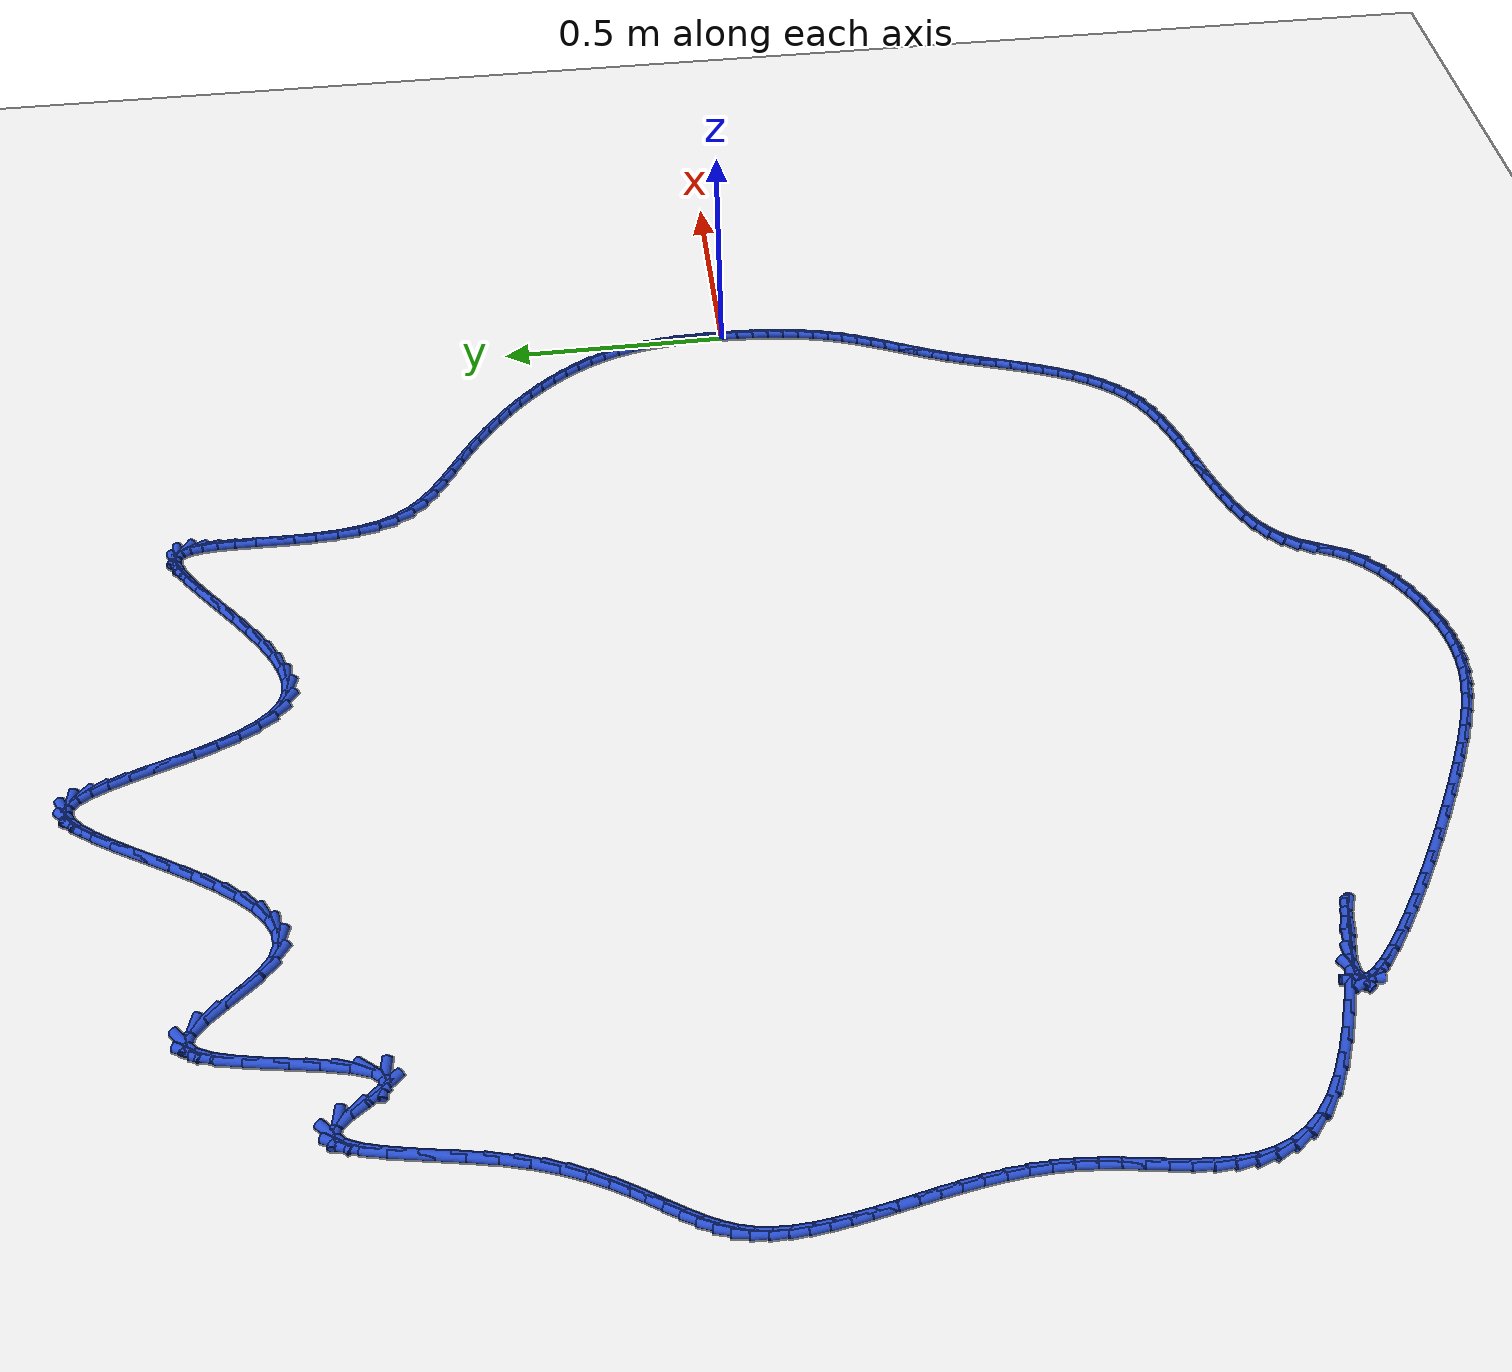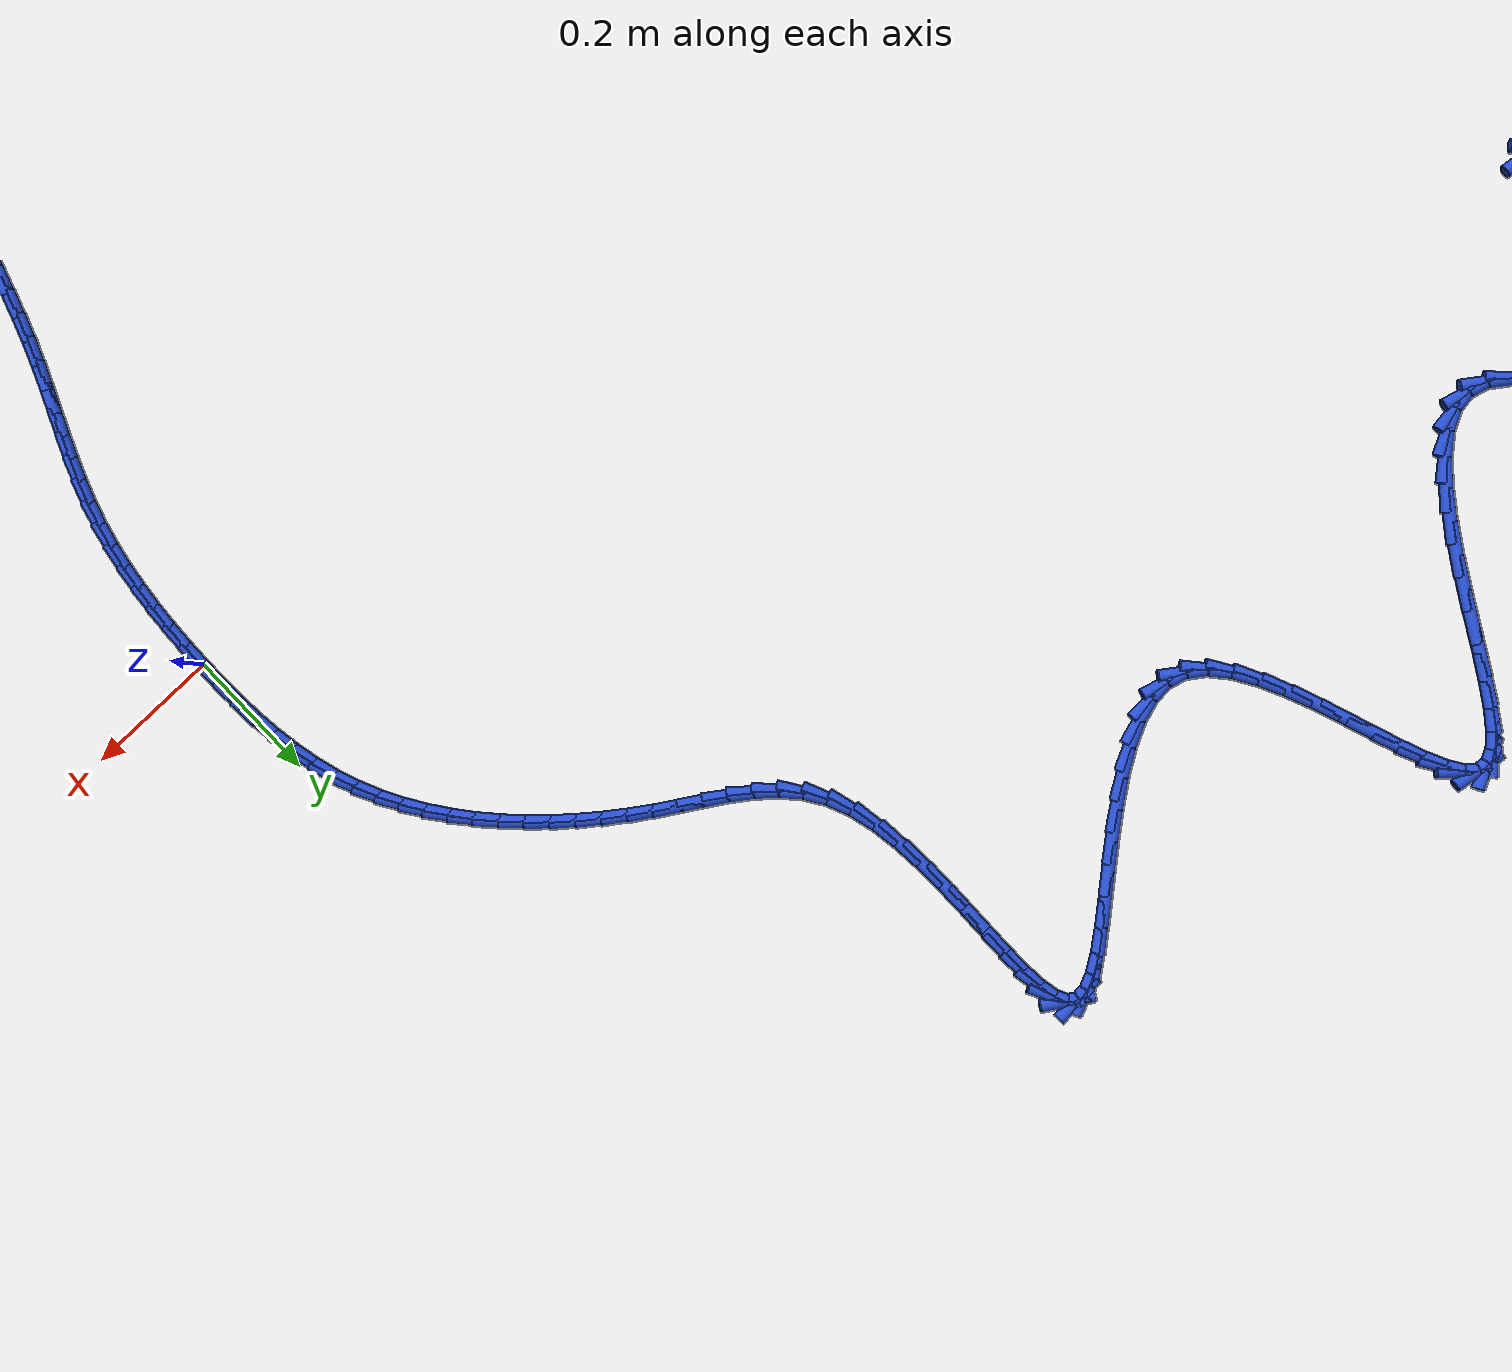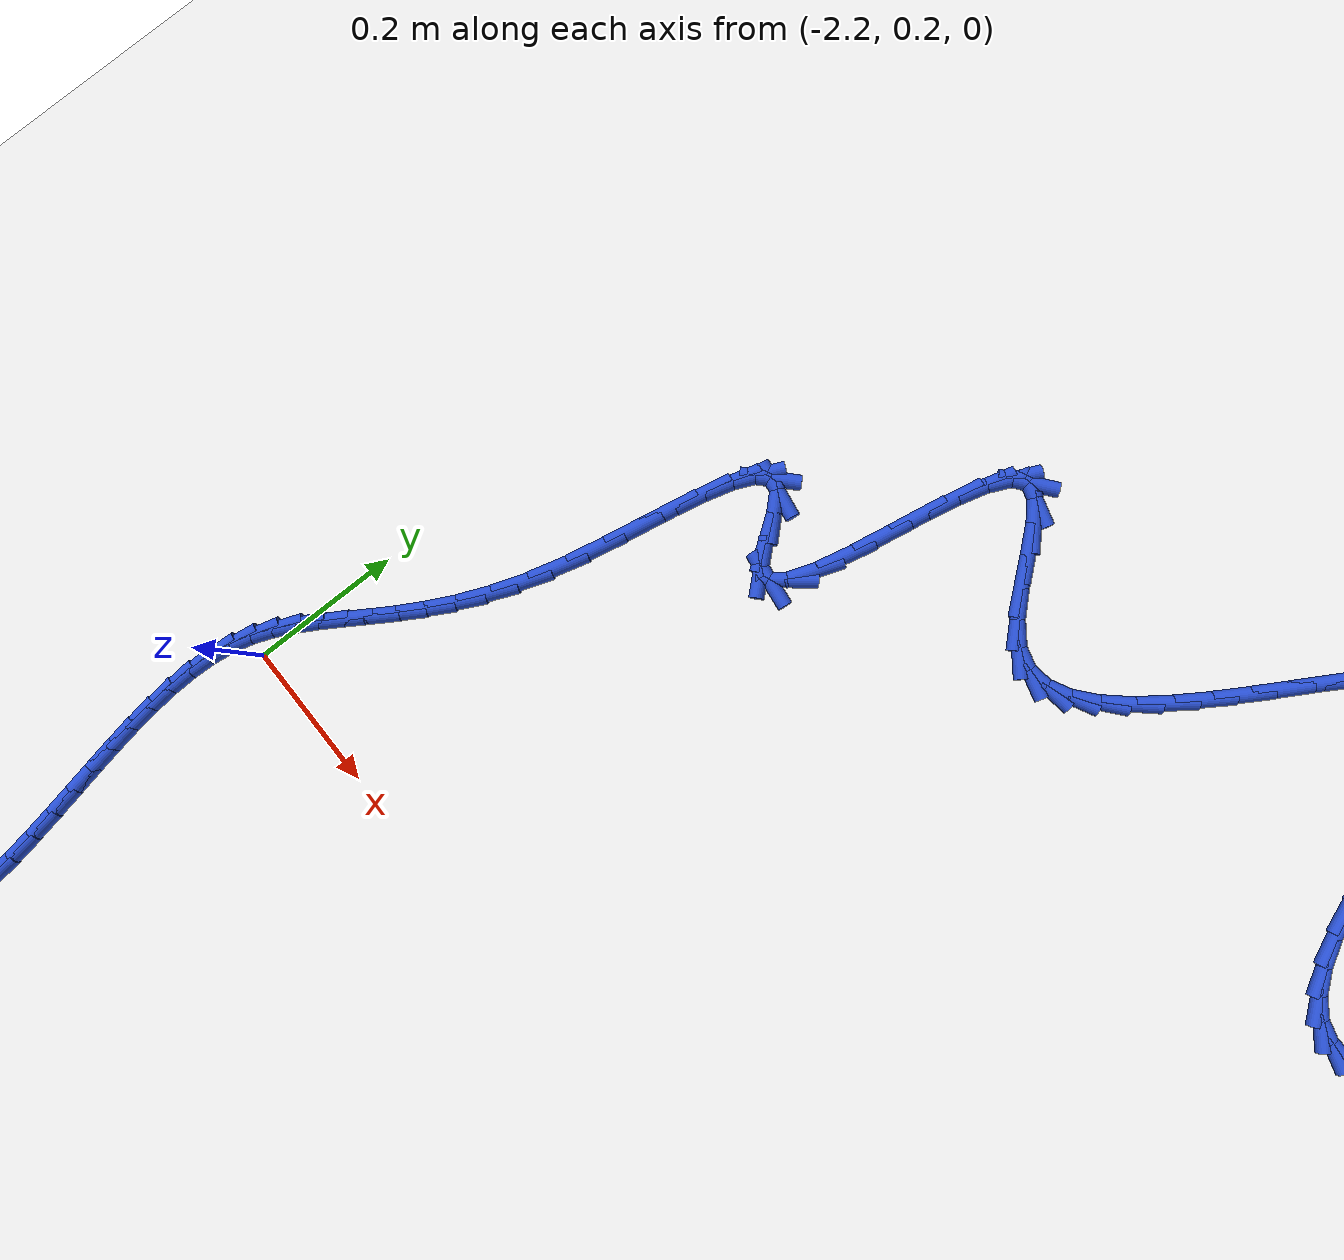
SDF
<sdf version="1.6">
 <world name="default">
  <light name="sun" type="directional">
   <pose>0 0 10 0 -0 0</pose>
   <diffuse>0.8 0.8 0.8 1</diffuse>
   <specular>0.2 0.2 0.2 1</specular>
   <attenuation>
    <range>1000</range>
    <constant>0.9</constant>
    <linear>0.01</linear>
    <quadratic>0.001</quadratic>
   </attenuation>
   <direction>-0.5 0.1 -0.9</direction>
  </light>
  <model name="ground_plane">
   <static>1</static>
   <link name="link">
    <collision name="collision">
     <geometry><plane><normal>0 0 1</normal><size>100 100</size></plane></geometry>
     <surface><friction><ode><mu>100</mu><mu2>50</mu2></ode></friction></surface>
    </collision>
    <visual name="visual">
     <cast_shadows>0</cast_shadows>
     <geometry><plane><normal>0 0 1</normal><size>100 100</size></plane></geometry>
     <material>
      <script><uri>file://media/materials/scripts/gazebo.material</uri><name>Gazebo/WhiteGlow</name></script>
     </material>
    </visual>
   </link>
  </model>
  <gravity>0 0 -9.8</gravity>
  <magnetic_field>6e-06 2.3e-05 -4.2e-05</magnetic_field>
  <atmosphere type="adiabatic"/>
  <physics name="default_physics" default="0" type="ode">
   <max_step_size>0.001</max_step_size>
   <real_time_factor>1</real_time_factor>
   <real_time_update_rate>1000</real_time_update_rate>
  </physics>
  <scene><ambient>0.4 0.4 0.4 1</ambient><background>0.7 0.7 0.7 1</background><shadows>1</shadows></scene>
  <spherical_coordinates>
   <surface_model>EARTH_WGS84</surface_model>
   <latitude_deg>0</latitude_deg>
   <longitude_deg>0</longitude_deg>
   <elevation>0</elevation>
   <heading_deg>0</heading_deg>
  </spherical_coordinates>
  <model name="line">
   <link name="link_0">
    <pose>-1.9081958235744878e-17 1.3877787807814457e-17 0.01 0 1.57 -1.569150691324924</pose>
    <collision name="collision">
     <geometry><cylinder><radius>0.01</radius><length>0.08</length></cylinder></geometry>
    </collision>
    <visual name="visual">
     <material>
      <script><name>Gazebo/Blue</name><uri>file://media/materials/scripts/gazebo.material</uri></script>
     </material>
     <geometry><cylinder><radius>0.01</radius><length>0.08</length></cylinder></geometry>
    </visual>
   </link>
   <link name="link_1">
    <pose>-5.93490348842549e-05 0.03606447624182651 0.01 0 1.57 -1.5408540072571866</pose>
    <collision name="collision">
     <geometry><cylinder><radius>0.01</radius><length>0.08</length></cylinder></geometry>
    </collision>
    <visual name="visual">
     <material>
      <script><name>Gazebo/Blue</name><uri>file://media/materials/scripts/gazebo.material</uri></script>
     </material>
     <geometry><cylinder><radius>0.01</radius><length>0.08</length></cylinder></geometry>
    </visual>
   </link>
   <link name="link_2">
    <pose>-0.0011372189621542512 0.07205192831365248 0.01 0 1.57 -1.5059572041774045</pose>
    <collision name="collision">
     <geometry><cylinder><radius>0.01</radius><length>0.08</length></cylinder></geometry>
    </collision>
    <visual name="visual">
     <material>
      <script><name>Gazebo/Blue</name><uri>file://media/materials/scripts/gazebo.material</uri></script>
     </material>
     <geometry><cylinder><radius>0.01</radius><length>0.08</length></cylinder></geometry>
    </visual>
   </link>
   <link name="link_3">
    <pose>-0.003459952128827188 0.10782473260817574 0.01 0 1.57 -1.4640918692509997</pose>
    <collision name="collision">
     <geometry><cylinder><radius>0.01</radius><length>0.08</length></cylinder></geometry>
    </collision>
    <visual name="visual">
     <material>
      <script><name>Gazebo/Blue</name><uri>file://media/materials/scripts/gazebo.material</uri></script>
     </material>
     <geometry><cylinder><radius>0.01</radius><length>0.08</length></cylinder></geometry>
    </visual>
   </link>
   <link name="link_4">
    <pose>-0.007253890881920242 0.14324526551809405 0.01 0 1.57 -1.4148614530525538</pose>
    <collision name="collision">
     <geometry><cylinder><radius>0.01</radius><length>0.08</length></cylinder></geometry>
    </collision>
    <visual name="visual">
     <material>
      <script><name>Gazebo/Blue</name><uri>file://media/materials/scripts/gazebo.material</uri></script>
     </material>
     <geometry><cylinder><radius>0.01</radius><length>0.08</length></cylinder></geometry>
    </visual>
   </link>
   <link name="link_5">
    <pose>-0.012745377568450594 0.1781759034361053 0.01 0 1.57 -1.3579001338973513</pose>
    <collision name="collision">
     <geometry><cylinder><radius>0.01</radius><length>0.08</length></cylinder></geometry>
    </collision>
    <visual name="visual">
     <material>
      <script><name>Gazebo/Blue</name><uri>file://media/materials/scripts/gazebo.material</uri></script>
     </material>
     <geometry><cylinder><radius>0.01</radius><length>0.08</length></cylinder></geometry>
    </visual>
   </link>
   <link name="link_6">
    <pose>-0.020160754535435435 0.21247902275490732 0.01 0 1.57 -1.2929562519048643</pose>
    <collision name="collision">
     <geometry><cylinder><radius>0.01</radius><length>0.08</length></cylinder></geometry>
    </collision>
    <visual name="visual">
     <material>
      <script><name>Gazebo/Blue</name><uri>file://media/materials/scripts/gazebo.material</uri></script>
     </material>
     <geometry><cylinder><radius>0.01</radius><length>0.08</length></cylinder></geometry>
    </visual>
   </link>
   <link name="link_7">
    <pose>-0.02972636412989191 0.2460169998671978 0.01 0 1.57 -1.2204378760313082</pose>
    <collision name="collision">
     <geometry><cylinder><radius>0.01</radius><length>0.08</length></cylinder></geometry>
    </collision>
    <visual name="visual">
     <material>
      <script><name>Gazebo/Blue</name><uri>file://media/materials/scripts/gazebo.material</uri></script>
     </material>
     <geometry><cylinder><radius>0.01</radius><length>0.08</length></cylinder></geometry>
    </visual>
   </link>
   <link name="link_8">
    <pose>-0.041654253718880825 0.27865727076518504 0.01 0 1.57 -1.1468807612114151</pose>
    <collision name="collision">
     <geometry><cylinder><radius>0.01</radius><length>0.08</length></cylinder></geometry>
    </collision>
    <visual name="visual">
     <material>
      <script><name>Gazebo/Blue</name><uri>file://media/materials/scripts/gazebo.material</uri></script>
     </material>
     <geometry><cylinder><radius>0.01</radius><length>0.08</length></cylinder></geometry>
    </visual>
   </link>
   <link name="link_9">
    <pose>-0.05595181602787426 0.3103397073960449 0.01 0 1.57 -1.0773373245273545</pose>
    <collision name="collision">
     <geometry><cylinder><radius>0.01</radius><length>0.08</length></cylinder></geometry>
    </collision>
    <visual name="visual">
     <material>
      <script><name>Gazebo/Blue</name><uri>file://media/materials/scripts/gazebo.material</uri></script>
     </material>
     <geometry><cylinder><radius>0.01</radius><length>0.08</length></cylinder></geometry>
    </visual>
   </link>
   <link name="link_10">
    <pose>-0.07247349649613222 0.341058316236473 0.01 0 1.57 -1.012130288703366</pose>
    <collision name="collision">
     <geometry><cylinder><radius>0.01</radius><length>0.08</length></cylinder></geometry>
    </collision>
    <visual name="visual">
     <material>
      <script><name>Gazebo/Blue</name><uri>file://media/materials/scripts/gazebo.material</uri></script>
     </material>
     <geometry><cylinder><radius>0.01</radius><length>0.08</length></cylinder></geometry>
    </visual>
   </link>
   <link name="link_11">
    <pose>-0.09107006279133989 0.37080840548246186 0.01 0 1.57 -0.9512995171308045</pose>
    <collision name="collision">
     <geometry><cylinder><radius>0.01</radius><length>0.08</length></cylinder></geometry>
    </collision>
    <visual name="visual">
     <material>
      <script><name>Gazebo/Blue</name><uri>file://media/materials/scripts/gazebo.material</uri></script>
     </material>
     <geometry><cylinder><radius>0.01</radius><length>0.08</length></cylinder></geometry>
    </visual>
   </link>
   <link name="link_12">
    <pose>-0.1115922825811826 0.3995852833300044 0.01 0 1.57 -0.894752493359129</pose>
    <collision name="collision">
     <geometry><cylinder><radius>0.01</radius><length>0.08</length></cylinder></geometry>
    </collision>
    <visual name="visual">
     <material>
      <script><name>Gazebo/Blue</name><uri>file://media/materials/scripts/gazebo.material</uri></script>
     </material>
     <geometry><cylinder><radius>0.01</radius><length>0.08</length></cylinder></geometry>
    </visual>
   </link>
   <link name="link_13">
    <pose>-0.13389092353334547 0.42738425797509294 0.01 0 1.57 -0.8423020565817934</pose>
    <collision name="collision">
     <geometry><cylinder><radius>0.01</radius><length>0.08</length></cylinder></geometry>
    </collision>
    <visual name="visual">
     <material>
      <script><name>Gazebo/Blue</name><uri>file://media/materials/scripts/gazebo.material</uri></script>
     </material>
     <geometry><cylinder><radius>0.01</radius><length>0.08</length></cylinder></geometry>
    </visual>
   </link>
   <link name="link_14">
    <pose>-0.15781675331551376 0.4542006376137204 0.01 0 1.57 -0.7936994102972715</pose>
    <collision name="collision">
     <geometry><cylinder><radius>0.01</radius><length>0.08</length></cylinder></geometry>
    </collision>
    <visual name="visual">
     <material>
      <script><name>Gazebo/Blue</name><uri>file://media/materials/scripts/gazebo.material</uri></script>
     </material>
     <geometry><cylinder><radius>0.01</radius><length>0.08</length></cylinder></geometry>
    </visual>
   </link>
   <link name="link_15">
    <pose>-0.1832205395953728 0.48002973044187947 0.01 0 1.57 -0.7486605788193607</pose>
    <collision name="collision">
     <geometry><cylinder><radius>0.01</radius><length>0.08</length></cylinder></geometry>
    </collision>
    <visual name="visual">
     <material>
      <script><name>Gazebo/Blue</name><uri>file://media/materials/scripts/gazebo.material</uri></script>
     </material>
     <geometry><cylinder><radius>0.01</radius><length>0.08</length></cylinder></geometry>
    </visual>
   </link>
   <link name="link_16">
    <pose>-0.20995305004060769 0.5048668446555626 0.01 0 1.57 -0.7068861418542753</pose>
    <collision name="collision">
     <geometry><cylinder><radius>0.01</radius><length>0.08</length></cylinder></geometry>
    </collision>
    <visual name="visual">
     <material>
      <script><name>Gazebo/Blue</name><uri>file://media/materials/scripts/gazebo.material</uri></script>
     </material>
     <geometry><cylinder><radius>0.01</radius><length>0.08</length></cylinder></geometry>
    </visual>
   </link>
   <link name="link_17">
    <pose>-0.23786505231890365 0.5287072884507623 0.01 0 1.57 -0.668074988446682</pose>
    <collision name="collision">
     <geometry><cylinder><radius>0.01</radius><length>0.08</length></cylinder></geometry>
    </collision>
    <visual name="visual">
     <material>
      <script><name>Gazebo/Blue</name><uri>file://media/materials/scripts/gazebo.material</uri></script>
     </material>
     <geometry><cylinder><radius>0.01</radius><length>0.08</length></cylinder></geometry>
    </visual>
   </link>
   <link name="link_18">
    <pose>-0.266807314097946 0.5515463700234716 0.01 0 1.57 -0.6319331916607651</pose>
    <collision name="collision">
     <geometry><cylinder><radius>0.01</radius><length>0.08</length></cylinder></geometry>
    </collision>
    <visual name="visual">
     <material>
      <script><name>Gazebo/Blue</name><uri>file://media/materials/scripts/gazebo.material</uri></script>
     </material>
     <geometry><cylinder><radius>0.01</radius><length>0.08</length></cylinder></geometry>
    </visual>
   </link>
   <link name="link_19">
    <pose>-0.29663060304541994 0.5733793975696829 0.01 0 1.57 -0.5981791291737039</pose>
    <collision name="collision">
     <geometry><cylinder><radius>0.01</radius><length>0.08</length></cylinder></geometry>
    </collision>
    <visual name="visual">
     <material>
      <script><name>Gazebo/Blue</name><uri>file://media/materials/scripts/gazebo.material</uri></script>
     </material>
     <geometry><cylinder><radius>0.01</radius><length>0.08</length></cylinder></geometry>
    </visual>
   </link>
   <link name="link_20">
    <pose>-0.3271856868290107 0.594201679285389 0.01 0 1.57 -0.566697601157017</pose>
    <collision name="collision">
     <geometry><cylinder><radius>0.01</radius><length>0.08</length></cylinder></geometry>
    </collision>
    <visual name="visual">
     <material>
      <script><name>Gazebo/Blue</name><uri>file://media/materials/scripts/gazebo.material</uri></script>
     </material>
     <geometry><cylinder><radius>0.01</radius><length>0.08</length></cylinder></geometry>
    </visual>
   </link>
   <link name="link_21">
    <pose>-0.35832002851226646 0.6140130592247995 0.01 0 1.57 -0.5486065865079678</pose>
    <collision name="collision">
     <geometry><cylinder><radius>0.01</radius><length>0.08</length></cylinder></geometry>
    </collision>
    <visual name="visual">
     <material>
      <script><name>Gazebo/Blue</name><uri>file://media/materials/scripts/gazebo.material</uri></script>
     </material>
     <geometry><cylinder><radius>0.01</radius><length>0.08</length></cylinder></geometry>
    </visual>
   </link>
   <link name="link_22">
    <pose>-0.389634353394275 0.633152050604905 0.01 0 1.57 -0.5631857956983269</pose>
    <collision name="collision">
     <geometry><cylinder><radius>0.01</radius><length>0.08</length></cylinder></geometry>
    </collision>
    <visual name="visual">
     <material>
      <script><name>Gazebo/Blue</name><uri>file://media/materials/scripts/gazebo.material</uri></script>
     </material>
     <geometry><cylinder><radius>0.01</radius><length>0.08</length></cylinder></geometry>
    </visual>
   </link>
   <link name="link_23">
    <pose>-0.4203161210820322 0.6525244099516091 0.01 0 1.57 -0.6136507816888855</pose>
    <collision name="collision">
     <geometry><cylinder><radius>0.01</radius><length>0.08</length></cylinder></geometry>
    </collision>
    <visual name="visual">
     <material>
      <script><name>Gazebo/Blue</name><uri>file://media/materials/scripts/gazebo.material</uri></script>
     </material>
     <geometry><cylinder><radius>0.01</radius><length>0.08</length></cylinder></geometry>
    </visual>
   </link>
   <link name="link_24">
    <pose>-0.449513377822686 0.6730899920745204 0.01 0 1.57 -0.7020463870780098</pose>
    <collision name="collision">
     <geometry><cylinder><radius>0.01</radius><length>0.08</length></cylinder></geometry>
    </collision>
    <visual name="visual">
     <material>
      <script><name>Gazebo/Blue</name><uri>file://media/materials/scripts/gazebo.material</uri></script>
     </material>
     <geometry><cylinder><radius>0.01</radius><length>0.08</length></cylinder></geometry>
    </visual>
   </link>
   <link name="link_25">
    <pose>-0.47637416986338416 0.6958086517832456 0.01 0 1.57 -0.8289876168616216</pose>
    <collision name="collision">
     <geometry><cylinder><radius>0.01</radius><length>0.08</length></cylinder></geometry>
    </collision>
    <visual name="visual">
     <material>
      <script><name>Gazebo/Blue</name><uri>file://media/materials/scripts/gazebo.material</uri></script>
     </material>
     <geometry><cylinder><radius>0.01</radius><length>0.08</length></cylinder></geometry>
    </visual>
   </link>
   <link name="link_26">
    <pose>-0.5000465434512743 0.721640243887393 0.01 0 1.57 -0.9898704752180619</pose>
    <collision name="collision">
     <geometry><cylinder><radius>0.01</radius><length>0.08</length></cylinder></geometry>
    </collision>
    <visual name="visual">
     <material>
      <script><name>Gazebo/Blue</name><uri>file://media/materials/scripts/gazebo.material</uri></script>
     </material>
     <geometry><cylinder><radius>0.01</radius><length>0.08</length></cylinder></geometry>
    </visual>
   </link>
   <link name="link_27">
    <pose>-0.5196785448335044 0.7515446231965703 0.01 0 1.57 -1.167995326273967</pose>
    <collision name="collision">
     <geometry><cylinder><radius>0.01</radius><length>0.08</length></cylinder></geometry>
    </collision>
    <visual name="visual">
     <material>
      <script><name>Gazebo/Blue</name><uri>file://media/materials/scripts/gazebo.material</uri></script>
     </material>
     <geometry><cylinder><radius>0.01</radius><length>0.08</length></cylinder></geometry>
    </visual>
   </link>
   <link name="link_28">
    <pose>-0.5345123991988237 0.7863578008443877 0.01 0 1.57 -1.3154110028252621</pose>
    <collision name="collision">
     <geometry><cylinder><radius>0.01</radius><length>0.08</length></cylinder></geometry>
    </collision>
    <visual name="visual">
     <material>
      <script><name>Gazebo/Blue</name><uri>file://media/materials/scripts/gazebo.material</uri></script>
     </material>
     <geometry><cylinder><radius>0.01</radius><length>0.08</length></cylinder></geometry>
    </visual>
   </link>
   <link name="link_29">
    <pose>-0.5447664202226732 0.8256322485209764 0.01 0 1.57 -1.4198193740194556</pose>
    <collision name="collision">
     <geometry><cylinder><radius>0.01</radius><length>0.08</length></cylinder></geometry>
    </collision>
    <visual name="visual">
     <material>
      <script><name>Gazebo/Blue</name><uri>file://media/materials/scripts/gazebo.material</uri></script>
     </material>
     <geometry><cylinder><radius>0.01</radius><length>0.08</length></cylinder></geometry>
    </visual>
   </link>
   <link name="link_30">
    <pose>-0.5512365049749113 0.8681609257628657 0.01 0 1.57 -1.4926543325168504</pose>
    <collision name="collision">
     <geometry><cylinder><radius>0.01</radius><length>0.08</length></cylinder></geometry>
    </collision>
    <visual name="visual">
     <material>
      <script><name>Gazebo/Blue</name><uri>file://media/materials/scripts/gazebo.material</uri></script>
     </material>
     <geometry><cylinder><radius>0.01</radius><length>0.08</length></cylinder></geometry>
    </visual>
   </link>
   <link name="link_31">
    <pose>-0.554726083556173 0.9127268863016678 0.01 0 1.57 -1.5418859090628172</pose>
    <collision name="collision">
     <geometry><cylinder><radius>0.01</radius><length>0.08</length></cylinder></geometry>
    </collision>
    <visual name="visual">
     <material>
      <script><name>Gazebo/Blue</name><uri>file://media/materials/scripts/gazebo.material</uri></script>
     </material>
     <geometry><cylinder><radius>0.01</radius><length>0.08</length></cylinder></geometry>
    </visual>
   </link>
   <link name="link_32">
    <pose>-0.5560385860670943 0.9581131838689949 0.01 0 1.57 1.5694372726779966</pose>
    <collision name="collision">
     <geometry><cylinder><radius>0.01</radius><length>0.08</length></cylinder></geometry>
    </collision>
    <visual name="visual">
     <material>
      <script><name>Gazebo/Blue</name><uri>file://media/materials/scripts/gazebo.material</uri></script>
     </material>
     <geometry><cylinder><radius>0.01</radius><length>0.08</length></cylinder></geometry>
    </visual>
   </link>
   <link name="link_33">
    <pose>-0.5559774426083103 1.003102872196458 0.01 0 1.57 1.5562419000715164</pose>
    <collision name="collision">
     <geometry><cylinder><radius>0.01</radius><length>0.08</length></cylinder></geometry>
    </collision>
    <visual name="visual">
     <material>
      <script><name>Gazebo/Blue</name><uri>file://media/materials/scripts/gazebo.material</uri></script>
     </material>
     <geometry><cylinder><radius>0.01</radius><length>0.08</length></cylinder></geometry>
    </visual>
   </link>
   <link name="link_34">
    <pose>-0.5553460832804563 1.0464790050156694 0.01 0 1.57 1.5609769630410781</pose>
    <collision name="collision">
     <geometry><cylinder><radius>0.01</radius><length>0.08</length></cylinder></geometry>
    </collision>
    <visual name="visual">
     <material>
      <script><name>Gazebo/Blue</name><uri>file://media/materials/scripts/gazebo.material</uri></script>
     </material>
     <geometry><cylinder><radius>0.01</radius><length>0.08</length></cylinder></geometry>
    </visual>
   </link>
   <link name="link_35">
    <pose>-0.5549479381841682 1.0870246360582414 0.01 0 1.57 -1.5533041104709742</pose>
    <collision name="collision">
     <geometry><cylinder><radius>0.01</radius><length>0.08</length></cylinder></geometry>
    </collision>
    <visual name="visual">
     <material>
      <script><name>Gazebo/Blue</name><uri>file://media/materials/scripts/gazebo.material</uri></script>
     </material>
     <geometry><cylinder><radius>0.01</radius><length>0.08</length></cylinder></geometry>
    </visual>
   </link>
   <link name="link_36">
    <pose>-0.5555864374200812 1.1235228190557849 0.01 0 1.57 -1.4916067513482636</pose>
    <collision name="collision">
     <geometry><cylinder><radius>0.01</radius><length>0.08</length></cylinder></geometry>
    </collision>
    <visual name="visual">
     <material>
      <script><name>Gazebo/Blue</name><uri>file://media/materials/scripts/gazebo.material</uri></script>
     </material>
     <geometry><cylinder><radius>0.01</radius><length>0.08</length></cylinder></geometry>
    </visual>
   </link>
   <link name="link_37">
    <pose>-0.5580650110888308 1.1547566077399125 0.01 0 1.57 -1.3667441756278378</pose>
    <collision name="collision">
     <geometry><cylinder><radius>0.01</radius><length>0.08</length></cylinder></geometry>
    </collision>
    <visual name="visual">
     <material>
      <script><name>Gazebo/Blue</name><uri>file://media/materials/scripts/gazebo.material</uri></script>
     </material>
     <geometry><cylinder><radius>0.01</radius><length>0.08</length></cylinder></geometry>
    </visual>
   </link>
   <link name="link_38">
    <pose>-0.5631870892910523 1.1795090558422356 0.01 0 1.57 -1.105183639330089</pose>
    <collision name="collision">
     <geometry><cylinder><radius>0.01</radius><length>0.08</length></cylinder></geometry>
    </collision>
    <visual name="visual">
     <material>
      <script><name>Gazebo/Blue</name><uri>file://media/materials/scripts/gazebo.material</uri></script>
     </material>
     <geometry><cylinder><radius>0.01</radius><length>0.08</length></cylinder></geometry>
    </visual>
   </link>
   <link name="link_39">
    <pose>-0.5717561021273814 1.1965632170943665 0.01 0 1.57 -0.5656851563280066</pose>
    <collision name="collision">
     <geometry><cylinder><radius>0.01</radius><length>0.08</length></cylinder></geometry>
    </collision>
    <visual name="visual">
     <material>
      <script><name>Gazebo/Blue</name><uri>file://media/materials/scripts/gazebo.material</uri></script>
     </material>
     <geometry><cylinder><radius>0.01</radius><length>0.08</length></cylinder></geometry>
    </visual>
   </link>
   <link name="link_40">
    <pose>-0.5845754544402983 1.2047021949950043 0.01 0 1.57 0.08310487150110424</pose>
    <collision name="collision">
     <geometry><cylinder><radius>0.01</radius><length>0.08</length></cylinder></geometry>
    </collision>
    <visual name="visual">
     <material>
      <script><name>Gazebo/Blue</name><uri>file://media/materials/scripts/gazebo.material</uri></script>
     </material>
     <geometry><cylinder><radius>0.01</radius><length>0.08</length></cylinder></geometry>
    </visual>
   </link>
   <link name="link_41">
    <pose>-0.6021812904799191 1.2032356865902885 0.01 0 1.57 0.42419387838292544</pose>
    <collision name="collision">
     <geometry><cylinder><radius>0.01</radius><length>0.08</length></cylinder></geometry>
    </collision>
    <visual name="visual">
     <material>
      <script><name>Gazebo/Blue</name><uri>file://media/materials/scripts/gazebo.material</uri></script>
     </material>
     <geometry><cylinder><radius>0.01</radius><length>0.08</length></cylinder></geometry>
    </visual>
   </link>
   <link name="link_42">
    <pose>-0.6241829758284656 1.1932994556206564 0.01 0 1.57 0.5791119335519502</pose>
    <collision name="collision">
     <geometry><cylinder><radius>0.01</radius><length>0.08</length></cylinder></geometry>
    </collision>
    <visual name="visual">
     <material>
      <script><name>Gazebo/Blue</name><uri>file://media/materials/scripts/gazebo.material</uri></script>
     </material>
     <geometry><cylinder><radius>0.01</radius><length>0.08</length></cylinder></geometry>
    </visual>
   </link>
   <link name="link_43">
    <pose>-0.649989122312652 1.1764248184642894 0.01 0 1.57 0.6548128186955411</pose>
    <collision name="collision">
     <geometry><cylinder><radius>0.01</radius><length>0.08</length></cylinder></geometry>
    </collision>
    <visual name="visual">
     <material>
      <script><name>Gazebo/Blue</name><uri>file://media/materials/scripts/gazebo.material</uri></script>
     </material>
     <geometry><cylinder><radius>0.01</radius><length>0.08</length></cylinder></geometry>
    </visual>
   </link>
   <link name="link_44">
    <pose>-0.679008341759192 1.1541430914993682 0.01 0 1.57 0.6908100697643068</pose>
    <collision name="collision">
     <geometry><cylinder><radius>0.01</radius><length>0.08</length></cylinder></geometry>
    </collision>
    <visual name="visual">
     <material>
      <script><name>Gazebo/Blue</name><uri>file://media/materials/scripts/gazebo.material</uri></script>
     </material>
     <geometry><cylinder><radius>0.01</radius><length>0.08</length></cylinder></geometry>
    </visual>
   </link>
   <link name="link_45">
    <pose>-0.7106492459948 1.1279855911040753 0.01 0 1.57 0.7024462666055163</pose>
    <collision name="collision">
     <geometry><cylinder><radius>0.01</radius><length>0.08</length></cylinder></geometry>
    </collision>
    <visual name="visual">
     <material>
      <script><name>Gazebo/Blue</name><uri>file://media/materials/scripts/gazebo.material</uri></script>
     </material>
     <geometry><cylinder><radius>0.01</radius><length>0.08</length></cylinder></geometry>
    </visual>
   </link>
   <link name="link_46">
    <pose>-0.7443204468461889 1.0994836336565907 0.01 0 1.57 0.6956901455982073</pose>
    <collision name="collision">
     <geometry><cylinder><radius>0.01</radius><length>0.08</length></cylinder></geometry>
    </collision>
    <visual name="visual">
     <material>
      <script><name>Gazebo/Blue</name><uri>file://media/materials/scripts/gazebo.material</uri></script>
     </material>
     <geometry><cylinder><radius>0.01</radius><length>0.08</length></cylinder></geometry>
    </visual>
   </link>
   <link name="link_47">
    <pose>-0.7794305561400736 1.0701685355350967 0.01 0 1.57 0.6718654380980967</pose>
    <collision name="collision">
     <geometry><cylinder><radius>0.01</radius><length>0.08</length></cylinder></geometry>
    </collision>
    <visual name="visual">
     <material>
      <script><name>Gazebo/Blue</name><uri>file://media/materials/scripts/gazebo.material</uri></script>
     </material>
     <geometry><cylinder><radius>0.01</radius><length>0.08</length></cylinder></geometry>
    </visual>
   </link>
   <link name="link_48">
    <pose>-0.8153881857031674 1.0415716131177744 0.01 0 1.57 0.6289795646332477</pose>
    <collision name="collision">
     <geometry><cylinder><radius>0.01</radius><length>0.08</length></cylinder></geometry>
    </collision>
    <visual name="visual">
     <material>
      <script><name>Gazebo/Blue</name><uri>file://media/materials/scripts/gazebo.material</uri></script>
     </material>
     <geometry><cylinder><radius>0.01</radius><length>0.08</length></cylinder></geometry>
    </visual>
   </link>
   <link name="link_49">
    <pose>-0.8516019473621842 1.0152241827828052 0.01 0 1.57 0.5614514153373033</pose>
    <collision name="collision">
     <geometry><cylinder><radius>0.01</radius><length>0.08</length></cylinder></geometry>
    </collision>
    <visual name="visual">
     <material>
      <script><name>Gazebo/Blue</name><uri>file://media/materials/scripts/gazebo.material</uri></script>
     </material>
     <geometry><cylinder><radius>0.01</radius><length>0.08</length></cylinder></geometry>
    </visual>
   </link>
   <link name="link_50">
    <pose>-0.8874804529438383 0.9926575609083705 0.01 0 1.57 0.4585664651938671</pose>
    <collision name="collision">
     <geometry><cylinder><radius>0.01</radius><length>0.08</length></cylinder></geometry>
    </collision>
    <visual name="visual">
     <material>
      <script><name>Gazebo/Blue</name><uri>file://media/materials/scripts/gazebo.material</uri></script>
     </material>
     <geometry><cylinder><radius>0.01</radius><length>0.08</length></cylinder></geometry>
    </visual>
   </link>
   <link name="link_51">
    <pose>-0.9224323142748427 0.9754030638726515 0.01 0 1.57 0.3018759165477437</pose>
    <collision name="collision">
     <geometry><cylinder><radius>0.01</radius><length>0.08</length></cylinder></geometry>
    </collision>
    <visual name="visual">
     <material>
      <script><name>Gazebo/Blue</name><uri>file://media/materials/scripts/gazebo.material</uri></script>
     </material>
     <geometry><cylinder><radius>0.01</radius><length>0.08</length></cylinder></geometry>
    </visual>
   </link>
   <link name="link_52">
    <pose>-0.9558661431819123 0.9649920080538297 0.01 0 1.57 0.06491541904355166</pose>
    <collision name="collision">
     <geometry><cylinder><radius>0.01</radius><length>0.08</length></cylinder></geometry>
    </collision>
    <visual name="visual">
     <material>
      <script><name>Gazebo/Blue</name><uri>file://media/materials/scripts/gazebo.material</uri></script>
     </material>
     <geometry><cylinder><radius>0.01</radius><length>0.08</length></cylinder></geometry>
    </visual>
   </link>
   <link name="link_53">
    <pose>-0.9871905514917602 0.9629557098300862 0.01 0 1.57 -0.26773312363121343</pose>
    <collision name="collision">
     <geometry><cylinder><radius>0.01</radius><length>0.08</length></cylinder></geometry>
    </collision>
    <visual name="visual">
     <material>
      <script><name>Gazebo/Blue</name><uri>file://media/materials/scripts/gazebo.material</uri></script>
     </material>
     <geometry><cylinder><radius>0.01</radius><length>0.08</length></cylinder></geometry>
    </visual>
   </link>
   <link name="link_54">
    <pose>-1.0158187960517608 0.9708089856566822 0.01 0 1.57 -0.6133430454166195</pose>
    <collision name="collision">
     <geometry><cylinder><radius>0.01</radius><length>0.08</length></cylinder></geometry>
    </collision>
    <visual name="visual">
     <material>
      <script><name>Gazebo/Blue</name><uri>file://media/materials/scripts/gazebo.material</uri></script>
     </material>
     <geometry><cylinder><radius>0.01</radius><length>0.08</length></cylinder></geometry>
    </visual>
   </link>
   <link name="link_55">
    <pose>-1.0414970492469429 0.9888840779784157 0.01 0 1.57 -0.8587390230001272</pose>
    <collision name="collision">
     <geometry><cylinder><radius>0.01</radius><length>0.08</length></cylinder></geometry>
    </collision>
    <visual name="visual">
     <material>
      <script><name>Gazebo/Blue</name><uri>file://media/materials/scripts/gazebo.material</uri></script>
     </material>
     <geometry><cylinder><radius>0.01</radius><length>0.08</length></cylinder></geometry>
    </visual>
   </link>
   <link name="link_56">
    <pose>-1.0645213549467363 1.0155599898955874 0.01 0 1.57 -1.0165618677070125</pose>
    <collision name="collision">
     <geometry><cylinder><radius>0.01</radius><length>0.08</length></cylinder></geometry>
    </collision>
    <visual name="visual">
     <material>
      <script><name>Gazebo/Blue</name><uri>file://media/materials/scripts/gazebo.material</uri></script>
     </material>
     <geometry><cylinder><radius>0.01</radius><length>0.08</length></cylinder></geometry>
    </visual>
   </link>
   <link name="link_57">
    <pose>-1.0852392483053268 1.0490328184911082 0.01 0 1.57 -1.1170533272375265</pose>
    <collision name="collision">
     <geometry><cylinder><radius>0.01</radius><length>0.08</length></cylinder></geometry>
    </collision>
    <visual name="visual">
     <material>
      <script><name>Gazebo/Blue</name><uri>file://media/materials/scripts/gazebo.material</uri></script>
     </material>
     <geometry><cylinder><radius>0.01</radius><length>0.08</length></cylinder></geometry>
    </visual>
   </link>
   <link name="link_58">
    <pose>-1.103998264476901 1.0874986608478898 0.01 0 1.57 -1.1802788930008468</pose>
    <collision name="collision">
     <geometry><cylinder><radius>0.01</radius><length>0.08</length></cylinder></geometry>
    </collision>
    <visual name="visual">
     <material>
      <script><name>Gazebo/Blue</name><uri>file://media/materials/scripts/gazebo.material</uri></script>
     </material>
     <geometry><cylinder><radius>0.01</radius><length>0.08</length></cylinder></geometry>
    </visual>
   </link>
   <link name="link_59">
    <pose>-1.1211459386156457 1.1291536140488423 0.01 0 1.57 -1.2172544023720744</pose>
    <collision name="collision">
     <geometry><cylinder><radius>0.01</radius><length>0.08</length></cylinder></geometry>
    </collision>
    <visual name="visual">
     <material>
      <script><name>Gazebo/Blue</name><uri>file://media/materials/scripts/gazebo.material</uri></script>
     </material>
     <geometry><cylinder><radius>0.01</radius><length>0.08</length></cylinder></geometry>
    </visual>
   </link>
   <link name="link_60">
    <pose>-1.1370298058757466 1.1721937751768783 0.01 0 1.57 -1.2330750753418653</pose>
    <collision name="collision">
     <geometry><cylinder><radius>0.01</radius><length>0.08</length></cylinder></geometry>
    </collision>
    <visual name="visual">
     <material>
      <script><name>Gazebo/Blue</name><uri>file://media/materials/scripts/gazebo.material</uri></script>
     </material>
     <geometry><cylinder><radius>0.01</radius><length>0.08</length></cylinder></geometry>
    </visual>
   </link>
   <link name="link_61">
    <pose>-1.1519974014113905 1.2148152413149078 0.01 0 1.57 -1.2284159394660012</pose>
    <collision name="collision">
     <geometry><cylinder><radius>0.01</radius><length>0.08</length></cylinder></geometry>
    </collision>
    <visual name="visual">
     <material>
      <script><name>Gazebo/Blue</name><uri>file://media/materials/scripts/gazebo.material</uri></script>
     </material>
     <geometry><cylinder><radius>0.01</radius><length>0.08</length></cylinder></geometry>
    </visual>
   </link>
   <link name="link_62">
    <pose>-1.1663962603767635 1.2552141095458424 0.01 0 1.57 -1.1991208123888741</pose>
    <collision name="collision">
     <geometry><cylinder><radius>0.01</radius><length>0.08</length></cylinder></geometry>
    </collision>
    <visual name="visual">
     <material>
      <script><name>Gazebo/Blue</name><uri>file://media/materials/scripts/gazebo.material</uri></script>
     </material>
     <geometry><cylinder><radius>0.01</radius><length>0.08</length></cylinder></geometry>
    </visual>
   </link>
   <link name="link_63">
    <pose>-1.1805739179260528 1.2915864769525942 0.01 0 1.57 -1.1327968194230476</pose>
    <collision name="collision">
     <geometry><cylinder><radius>0.01</radius><length>0.08</length></cylinder></geometry>
    </collision>
    <visual name="visual">
     <material>
      <script><name>Gazebo/Blue</name><uri>file://media/materials/scripts/gazebo.material</uri></script>
     </material>
     <geometry><cylinder><radius>0.01</radius><length>0.08</length></cylinder></geometry>
    </visual>
   </link>
   <link name="link_64">
    <pose>-1.1948779092134438 1.3221284406180733 0.01 0 1.57 -0.9978694349605622</pose>
    <collision name="collision">
     <geometry><cylinder><radius>0.01</radius><length>0.08</length></cylinder></geometry>
    </collision>
    <visual name="visual">
     <material>
      <script><name>Gazebo/Blue</name><uri>file://media/materials/scripts/gazebo.material</uri></script>
     </material>
     <geometry><cylinder><radius>0.01</radius><length>0.08</length></cylinder></geometry>
    </visual>
   </link>
   <link name="link_65">
    <pose>-1.209655769393123 1.345036097625191 0.01 0 1.57 -0.712260491637571</pose>
    <collision name="collision">
     <geometry><cylinder><radius>0.01</radius><length>0.08</length></cylinder></geometry>
    </collision>
    <visual name="visual">
     <material>
      <script><name>Gazebo/Blue</name><uri>file://media/materials/scripts/gazebo.material</uri></script>
     </material>
     <geometry><cylinder><radius>0.01</radius><length>0.08</length></cylinder></geometry>
    </visual>
   </link>
   <link name="link_66">
    <pose>-1.2252550336192776 1.3585055450568584 0.01 0 1.57 -0.13491293261273546</pose>
    <collision name="collision">
     <geometry><cylinder><radius>0.01</radius><length>0.08</length></cylinder></geometry>
    </collision>
    <visual name="visual">
     <material>
      <script><name>Gazebo/Blue</name><uri>file://media/materials/scripts/gazebo.material</uri></script>
     </material>
     <geometry><cylinder><radius>0.01</radius><length>0.08</length></cylinder></geometry>
    </visual>
   </link>
   <link name="link_67">
    <pose>-1.2420175108924987 1.3607808414053937 0.01 0 1.57 0.4681121038624852</pose>
    <collision name="collision">
     <geometry><cylinder><radius>0.01</radius><length>0.08</length></cylinder></geometry>
    </collision>
    <visual name="visual">
     <material>
      <script><name>Gazebo/Blue</name><uri>file://media/materials/scripts/gazebo.material</uri></script>
     </material>
     <geometry><cylinder><radius>0.01</radius><length>0.08</length></cylinder></geometry>
    </visual>
   </link>
   <link name="link_68">
    <pose>-1.2601021859775083 1.3516373537249804 0.01 0 1.57 0.7755436263474716</pose>
    <collision name="collision">
     <geometry><cylinder><radius>0.01</radius><length>0.08</length></cylinder></geometry>
    </collision>
    <visual name="visual">
     <material>
      <script><name>Gazebo/Blue</name><uri>file://media/materials/scripts/gazebo.material</uri></script>
     </material>
     <geometry><cylinder><radius>0.01</radius><length>0.08</length></cylinder></geometry>
    </visual>
   </link>
   <link name="link_69">
    <pose>-1.2794512970190983 1.332665886466671 0.01 0 1.57 0.9222210425917697</pose>
    <collision name="collision">
     <geometry><cylinder><radius>0.01</radius><length>0.08</length></cylinder></geometry>
    </collision>
    <visual name="visual">
     <material>
      <script><name>Gazebo/Blue</name><uri>file://media/materials/scripts/gazebo.material</uri></script>
     </material>
     <geometry><cylinder><radius>0.01</radius><length>0.08</length></cylinder></geometry>
    </visual>
   </link>
   <link name="link_70">
    <pose>-1.2999945098607277 1.3055625478044337 0.01 0 1.57 0.9972230381803511</pose>
    <collision name="collision">
     <geometry><cylinder><radius>0.01</radius><length>0.08</length></cylinder></geometry>
    </collision>
    <visual name="visual">
     <material>
      <script><name>Gazebo/Blue</name><uri>file://media/materials/scripts/gazebo.material</uri></script>
     </material>
     <geometry><cylinder><radius>0.01</radius><length>0.08</length></cylinder></geometry>
    </visual>
   </link>
   <link name="link_71">
    <pose>-1.321661490345853 1.2720234459122393 0.01 0 1.57 1.0351318555374092</pose>
    <collision name="collision">
     <geometry><cylinder><radius>0.01</radius><length>0.08</length></cylinder></geometry>
    </collision>
    <visual name="visual">
     <material>
      <script><name>Gazebo/Blue</name><uri>file://media/materials/scripts/gazebo.material</uri></script>
     </material>
     <geometry><cylinder><radius>0.01</radius><length>0.08</length></cylinder></geometry>
    </visual>
   </link>
   <link name="link_72">
    <pose>-1.3443819043179324 1.2337446889640573 0.01 0 1.57 1.0499958867244734</pose>
    <collision name="collision">
     <geometry><cylinder><radius>0.01</radius><length>0.08</length></cylinder></geometry>
    </collision>
    <visual name="visual">
     <material>
      <script><name>Gazebo/Blue</name><uri>file://media/materials/scripts/gazebo.material</uri></script>
     </material>
     <geometry><cylinder><radius>0.01</radius><length>0.08</length></cylinder></geometry>
    </visual>
   </link>
   <link name="link_73">
    <pose>-1.368085417620423 1.192422385133857 0.01 0 1.57 1.0475334901209297</pose>
    <collision name="collision">
     <geometry><cylinder><radius>0.01</radius><length>0.08</length></cylinder></geometry>
    </collision>
    <visual name="visual">
     <material>
      <script><name>Gazebo/Blue</name><uri>file://media/materials/scripts/gazebo.material</uri></script>
     </material>
     <geometry><cylinder><radius>0.01</radius><length>0.08</length></cylinder></geometry>
    </visual>
   </link>
   <link name="link_74">
    <pose>-1.3927016960967837 1.149752642595607 0.01 0 1.57 1.0292297802257018</pose>
    <collision name="collision">
     <geometry><cylinder><radius>0.01</radius><length>0.08</length></cylinder></geometry>
    </collision>
    <visual name="visual">
     <material>
      <script><name>Gazebo/Blue</name><uri>file://media/materials/scripts/gazebo.material</uri></script>
     </material>
     <geometry><cylinder><radius>0.01</radius><length>0.08</length></cylinder></geometry>
    </visual>
   </link>
   <link name="link_75">
    <pose>-1.418160405590471 1.1074315695232793 0.01 0 1.57 0.9935277240687171</pose>
    <collision name="collision">
     <geometry><cylinder><radius>0.01</radius><length>0.08</length></cylinder></geometry>
    </collision>
    <visual name="visual">
     <material>
      <script><name>Gazebo/Blue</name><uri>file://media/materials/scripts/gazebo.material</uri></script>
     </material>
     <geometry><cylinder><radius>0.01</radius><length>0.08</length></cylinder></geometry>
    </visual>
   </link>
   <link name="link_76">
    <pose>-1.4443912119449431 1.0671552740908419 0.01 0 1.57 0.9355613469447946</pose>
    <collision name="collision">
     <geometry><cylinder><radius>0.01</radius><length>0.08</length></cylinder></geometry>
    </collision>
    <visual name="visual">
     <material>
      <script><name>Gazebo/Blue</name><uri>file://media/materials/scripts/gazebo.material</uri></script>
     </material>
     <geometry><cylinder><radius>0.01</radius><length>0.08</length></cylinder></geometry>
    </visual>
   </link>
   <link name="link_77">
    <pose>-1.4713237810036572 1.0306198644722648 0.01 0 1.57 0.8455755475601437</pose>
    <collision name="collision">
     <geometry><cylinder><radius>0.01</radius><length>0.08</length></cylinder></geometry>
    </collision>
    <visual name="visual">
     <material>
      <script><name>Gazebo/Blue</name><uri>file://media/materials/scripts/gazebo.material</uri></script>
     </material>
     <geometry><cylinder><radius>0.01</radius><length>0.08</length></cylinder></geometry>
    </visual>
   </link>
   <link name="link_78">
    <pose>-1.4988877786100718 0.9995214488415173 0.01 0 1.57 0.7057103649303414</pose>
    <collision name="collision">
     <geometry><cylinder><radius>0.01</radius><length>0.08</length></cylinder></geometry>
    </collision>
    <visual name="visual">
     <material>
      <script><name>Gazebo/Blue</name><uri>file://media/materials/scripts/gazebo.material</uri></script>
     </material>
     <geometry><cylinder><radius>0.01</radius><length>0.08</length></cylinder></geometry>
    </visual>
   </link>
   <link name="link_79">
    <pose>-1.5270128706076438 0.9755561353725697 0.01 0 1.57 0.4865316087695177</pose>
    <collision name="collision">
     <geometry><cylinder><radius>0.01</radius><length>0.08</length></cylinder></geometry>
    </collision>
    <visual name="visual">
     <material>
      <script><name>Gazebo/Blue</name><uri>file://media/materials/scripts/gazebo.material</uri></script>
     </material>
     <geometry><cylinder><radius>0.01</radius><length>0.08</length></cylinder></geometry>
    </visual>
   </link>
   <link name="link_80">
    <pose>-1.5556287228398313 0.9604200322393914 0.01 0 1.57 0.1574790720364575</pose>
    <collision name="collision">
     <geometry><cylinder><radius>0.01</radius><length>0.08</length></cylinder></geometry>
    </collision>
    <visual name="visual">
     <material>
      <script><name>Gazebo/Blue</name><uri>file://media/materials/scripts/gazebo.material</uri></script>
     </material>
     <geometry><cylinder><radius>0.01</radius><length>0.08</length></cylinder></geometry>
    </visual>
   </link>
   <link name="link_81">
    <pose>-1.5846650011500918 0.9558092476159517 0.01 0 1.57 -0.25341750664405466</pose>
    <collision name="collision">
     <geometry><cylinder><radius>0.01</radius><length>0.08</length></cylinder></geometry>
    </collision>
    <visual name="visual">
     <material>
      <script><name>Gazebo/Blue</name><uri>file://media/materials/scripts/gazebo.material</uri></script>
     </material>
     <geometry><cylinder><radius>0.01</radius><length>0.08</length></cylinder></geometry>
    </visual>
   </link>
   <link name="link_82">
    <pose>-1.6140513713818825 0.9634198896762205 0.01 0 1.57 -0.6122858602617444</pose>
    <collision name="collision">
     <geometry><cylinder><radius>0.01</radius><length>0.08</length></cylinder></geometry>
    </collision>
    <visual name="visual">
     <material>
      <script><name>Gazebo/Blue</name><uri>file://media/materials/scripts/gazebo.material</uri></script>
     </material>
     <geometry><cylinder><radius>0.01</radius><length>0.08</length></cylinder></geometry>
    </visual>
   </link>
   <link name="link_83">
    <pose>-1.6436547340356735 0.9842111242656744 0.01 0 1.57 -0.7968918434866407</pose>
    <collision name="collision">
     <geometry><cylinder><radius>0.01</radius><length>0.08</length></cylinder></geometry>
    </collision>
    <visual name="visual">
     <material>
      <script><name>Gazebo/Blue</name><uri>file://media/materials/scripts/gazebo.material</uri></script>
     </material>
     <geometry><cylinder><radius>0.01</radius><length>0.08</length></cylinder></geometry>
    </visual>
   </link>
   <link name="link_84">
    <pose>-1.6729171574557506 1.0141540651696352 0.01 0 1.57 -0.863854955197884</pose>
    <collision name="collision">
     <geometry><cylinder><radius>0.01</radius><length>0.08</length></cylinder></geometry>
    </collision>
    <visual name="visual">
     <material>
      <script><name>Gazebo/Blue</name><uri>file://media/materials/scripts/gazebo.material</uri></script>
     </material>
     <geometry><cylinder><radius>0.01</radius><length>0.08</length></cylinder></geometry>
    </visual>
   </link>
   <link name="link_85">
    <pose>-1.7011045710322492 1.0471517381995648 0.01 0 1.57 -0.8487117316933396</pose>
    <collision name="collision">
     <geometry><cylinder><radius>0.01</radius><length>0.08</length></cylinder></geometry>
    </collision>
    <visual name="visual">
     <material>
      <script><name>Gazebo/Blue</name><uri>file://media/materials/scripts/gazebo.material</uri></script>
     </material>
     <geometry><cylinder><radius>0.01</radius><length>0.08</length></cylinder></geometry>
    </visual>
   </link>
   <link name="link_86">
    <pose>-1.7274823371073071 1.0771005113259342 0.01 0 1.57 -0.7174487408556325</pose>
    <collision name="collision">
     <geometry><cylinder><radius>0.01</radius><length>0.08</length></cylinder></geometry>
    </collision>
    <visual name="visual">
     <material>
      <script><name>Gazebo/Blue</name><uri>file://media/materials/scripts/gazebo.material</uri></script>
     </material>
     <geometry><cylinder><radius>0.01</radius><length>0.08</length></cylinder></geometry>
    </visual>
   </link>
   <link name="link_87">
    <pose>-1.7513158180230595 1.0978967525192163 0.01 0 1.57 -0.26327473330158213</pose>
    <collision name="collision">
     <geometry><cylinder><radius>0.01</radius><length>0.08</length></cylinder></geometry>
    </collision>
    <visual name="visual">
     <material>
      <script><name>Gazebo/Blue</name><uri>file://media/materials/scripts/gazebo.material</uri></script>
     </material>
     <geometry><cylinder><radius>0.01</radius><length>0.08</length></cylinder></geometry>
    </visual>
   </link>
   <link name="link_88">
    <pose>-1.7718703784266927 1.1034368455784749 0.01 0 1.57 0.6916312635057502</pose>
    <collision name="collision">
     <geometry><cylinder><radius>0.01</radius><length>0.08</length></cylinder></geometry>
    </collision>
    <visual name="visual">
     <material>
      <script><name>Gazebo/Blue</name><uri>file://media/materials/scripts/gazebo.material</uri></script>
     </material>
     <geometry><cylinder><radius>0.01</radius><length>0.08</length></cylinder></geometry>
    </visual>
   </link>
   <link name="link_89">
    <pose>-1.7886871928999024 1.0895111399776398 0.01 0 1.57 1.1495705585999736</pose>
    <collision name="collision">
     <geometry><cylinder><radius>0.01</radius><length>0.08</length></cylinder></geometry>
    </collision>
    <visual name="visual">
     <material>
      <script><name>Gazebo/Blue</name><uri>file://media/materials/scripts/gazebo.material</uri></script>
     </material>
     <geometry><cylinder><radius>0.01</radius><length>0.08</length></cylinder></geometry>
    </visual>
   </link>
   <link name="link_90">
    <pose>-1.8023442384420425 1.059029627904575 0.01 0 1.57 1.3102470286061427</pose>
    <collision name="collision">
     <geometry><cylinder><radius>0.01</radius><length>0.08</length></cylinder></geometry>
    </collision>
    <visual name="visual">
     <material>
      <script><name>Gazebo/Blue</name><uri>file://media/materials/scripts/gazebo.material</uri></script>
     </material>
     <geometry><cylinder><radius>0.01</radius><length>0.08</length></cylinder></geometry>
    </visual>
   </link>
   <link name="link_91">
    <pose>-1.8136630721855485 1.0165749476465558 0.01 0 1.57 1.3766216972831664</pose>
    <collision name="collision">
     <geometry><cylinder><radius>0.01</radius><length>0.08</length></cylinder></geometry>
    </collision>
    <visual name="visual">
     <material>
      <script><name>Gazebo/Blue</name><uri>file://media/materials/scripts/gazebo.material</uri></script>
     </material>
     <geometry><cylinder><radius>0.01</radius><length>0.08</length></cylinder></geometry>
    </visual>
   </link>
   <link name="link_92">
    <pose>-1.8234652512628577 0.9667297374908578 0.01 0 1.57 1.3995270173779377</pose>
    <collision name="collision">
     <geometry><cylinder><radius>0.01</radius><length>0.08</length></cylinder></geometry>
    </collision>
    <visual name="visual">
     <material>
      <script><name>Gazebo/Blue</name><uri>file://media/materials/scripts/gazebo.material</uri></script>
     </material>
     <geometry><cylinder><radius>0.01</radius><length>0.08</length></cylinder></geometry>
    </visual>
   </link>
   <link name="link_93">
    <pose>-1.8325723328064065 0.9140766357247554 0.01 0 1.57 1.3912675946774518</pose>
    <collision name="collision">
     <geometry><cylinder><radius>0.01</radius><length>0.08</length></cylinder></geometry>
    </collision>
    <visual name="visual">
     <material>
      <script><name>Gazebo/Blue</name><uri>file://media/materials/scripts/gazebo.material</uri></script>
     </material>
     <geometry><cylinder><radius>0.01</radius><length>0.08</length></cylinder></geometry>
    </visual>
   </link>
   <link name="link_94">
    <pose>-1.8418058739486312 0.8631982806355251 0.01 0 1.57 1.3459712557685477</pose>
    <collision name="collision">
     <geometry><cylinder><radius>0.01</radius><length>0.08</length></cylinder></geometry>
    </collision>
    <visual name="visual">
     <material>
      <script><name>Gazebo/Blue</name><uri>file://media/materials/scripts/gazebo.material</uri></script>
     </material>
     <geometry><cylinder><radius>0.01</radius><length>0.08</length></cylinder></geometry>
    </visual>
   </link>
   <link name="link_95">
    <pose>-1.851987431821968 0.8186773105104419 0.01 0 1.57 1.2288837321542125</pose>
    <collision name="collision">
     <geometry><cylinder><radius>0.01</radius><length>0.08</length></cylinder></geometry>
    </collision>
    <visual name="visual">
     <material>
      <script><name>Gazebo/Blue</name><uri>file://media/materials/scripts/gazebo.material</uri></script>
     </material>
     <geometry><cylinder><radius>0.01</radius><length>0.08</length></cylinder></geometry>
    </visual>
   </link>
   <link name="link_96">
    <pose>-1.8639385635588532 0.7850963636367804 0.01 0 1.57 0.8928345228396772</pose>
    <collision name="collision">
     <geometry><cylinder><radius>0.01</radius><length>0.08</length></cylinder></geometry>
    </collision>
    <visual name="visual">
     <material>
      <script><name>Gazebo/Blue</name><uri>file://media/materials/scripts/gazebo.material</uri></script>
     </material>
     <geometry><cylinder><radius>0.01</radius><length>0.08</length></cylinder></geometry>
    </visual>
   </link>
   <link name="link_97">
    <pose>-1.8784808262917239 0.7670380783018171 0.01 0 1.57 -0.11351821959854738</pose>
    <collision name="collision">
     <geometry><cylinder><radius>0.01</radius><length>0.08</length></cylinder></geometry>
    </collision>
    <visual name="visual">
     <material>
      <script><name>Gazebo/Blue</name><uri>file://media/materials/scripts/gazebo.material</uri></script>
     </material>
     <geometry><cylinder><radius>0.01</radius><length>0.08</length></cylinder></geometry>
    </visual>
   </link>
   <link name="link_98">
    <pose>-1.8964357771530156 0.7690850927928266 0.01 0 1.57 -0.8301115718260607</pose>
    <collision name="collision">
     <geometry><cylinder><radius>0.01</radius><length>0.08</length></cylinder></geometry>
    </collision>
    <visual name="visual">
     <material>
      <script><name>Gazebo/Blue</name><uri>file://media/materials/scripts/gazebo.material</uri></script>
     </material>
     <geometry><cylinder><radius>0.01</radius><length>0.08</length></cylinder></geometry>
    </visual>
   </link>
   <link name="link_99">
    <pose>-1.9180705706299 0.7927465885867103 0.01 0 1.57 -0.9444646915819295</pose>
    <collision name="collision">
     <geometry><cylinder><radius>0.01</radius><length>0.08</length></cylinder></geometry>
    </collision>
    <visual name="visual">
     <material>
      <script><name>Gazebo/Blue</name><uri>file://media/materials/scripts/gazebo.material</uri></script>
     </material>
     <geometry><cylinder><radius>0.01</radius><length>0.08</length></cylinder></geometry>
    </visual>
   </link>
   <link name="link_100">
    <pose>-1.940906450540544 0.8243091685554468 0.01 0 1.57 -0.7995409919296418</pose>
    <collision name="collision">
     <geometry><cylinder><radius>0.01</radius><length>0.08</length></cylinder></geometry>
    </collision>
    <visual name="visual">
     <material>
      <script><name>Gazebo/Blue</name><uri>file://media/materials/scripts/gazebo.material</uri></script>
     </material>
     <geometry><cylinder><radius>0.01</radius><length>0.08</length></cylinder></geometry>
    </visual>
   </link>
   <link name="link_101">
    <pose>-1.9616764952581485 0.8456751759686302 0.01 0 1.57 -0.1486984555540658</pose>
    <collision name="collision">
     <geometry><cylinder><radius>0.01</radius><length>0.08</length></cylinder></geometry>
    </collision>
    <visual name="visual">
     <material>
      <script><name>Gazebo/Blue</name><uri>file://media/materials/scripts/gazebo.material</uri></script>
     </material>
     <geometry><cylinder><radius>0.01</radius><length>0.08</length></cylinder></geometry>
    </visual>
   </link>
   <link name="link_102">
    <pose>-1.9789089813702403 0.8482566748507379 0.01 0 1.57 0.7721833318407554</pose>
    <collision name="collision">
     <geometry><cylinder><radius>0.01</radius><length>0.08</length></cylinder></geometry>
    </collision>
    <visual name="visual">
     <material>
      <script><name>Gazebo/Blue</name><uri>file://media/materials/scripts/gazebo.material</uri></script>
     </material>
     <geometry><cylinder><radius>0.01</radius><length>0.08</length></cylinder></geometry>
    </visual>
   </link>
   <link name="link_103">
    <pose>-1.9931870528147042 0.8343510676537846 0.01 0 1.57 1.1587322378153986</pose>
    <collision name="collision">
     <geometry><cylinder><radius>0.01</radius><length>0.08</length></cylinder></geometry>
    </collision>
    <visual name="visual">
     <material>
      <script><name>Gazebo/Blue</name><uri>file://media/materials/scripts/gazebo.material</uri></script>
     </material>
     <geometry><cylinder><radius>0.01</radius><length>0.08</length></cylinder></geometry>
    </visual>
   </link>
   <link name="link_104">
    <pose>-2.0052064510558885 0.806852224617081 0.01 0 1.57 1.3035997404386308</pose>
    <collision name="collision">
     <geometry><cylinder><radius>0.01</radius><length>0.08</length></cylinder></geometry>
    </collision>
    <visual name="visual">
     <material>
      <script><name>Gazebo/Blue</name><uri>file://media/materials/scripts/gazebo.material</uri></script>
     </material>
     <geometry><cylinder><radius>0.01</radius><length>0.08</length></cylinder></geometry>
    </visual>
   </link>
   <link name="link_105">
    <pose>-2.015662917558142 0.7686540159799391 0.01 0 1.57 1.3652932069871788</pose>
    <collision name="collision">
     <geometry><cylinder><radius>0.01</radius><length>0.08</length></cylinder></geometry>
    </collision>
    <visual name="visual">
     <material>
      <script><name>Gazebo/Blue</name><uri>file://media/materials/scripts/gazebo.material</uri></script>
     </material>
     <geometry><cylinder><radius>0.01</radius><length>0.08</length></cylinder></geometry>
    </visual>
   </link>
   <link name="link_106">
    <pose>-2.025252193785814 0.7226503119816704 0.01 0 1.57 1.387893207308037</pose>
    <collision name="collision">
     <geometry><cylinder><radius>0.01</radius><length>0.08</length></cylinder></geometry>
    </collision>
    <visual name="visual">
     <material>
      <script><name>Gazebo/Blue</name><uri>file://media/materials/scripts/gazebo.material</uri></script>
     </material>
     <geometry><cylinder><radius>0.01</radius><length>0.08</length></cylinder></geometry>
    </visual>
   </link>
   <link name="link_107">
    <pose>-2.034670021203253 0.6717349828615861 0.01 0 1.57 1.3851350978244776</pose>
    <collision name="collision">
     <geometry><cylinder><radius>0.01</radius><length>0.08</length></cylinder></geometry>
    </collision>
    <visual name="visual">
     <material>
      <script><name>Gazebo/Blue</name><uri>file://media/materials/scripts/gazebo.material</uri></script>
     </material>
     <geometry><cylinder><radius>0.01</radius><length>0.08</length></cylinder></geometry>
    </visual>
   </link>
   <link name="link_108">
    <pose>-2.0446121412748073 0.6188018988589968 0.01 0 1.57 1.3595727891873166</pose>
    <collision name="collision">
     <geometry><cylinder><radius>0.01</radius><length>0.08</length></cylinder></geometry>
    </collision>
    <visual name="visual">
     <material>
      <script><name>Gazebo/Blue</name><uri>file://media/materials/scripts/gazebo.material</uri></script>
     </material>
     <geometry><cylinder><radius>0.01</radius><length>0.08</length></cylinder></geometry>
    </visual>
   </link>
   <link name="link_109">
    <pose>-2.0557742954648264 0.5667449302132156 0.01 0 1.57 1.3070940769769754</pose>
    <collision name="collision">
     <geometry><cylinder><radius>0.01</radius><length>0.08</length></cylinder></geometry>
    </collision>
    <visual name="visual">
     <material>
      <script><name>Gazebo/Blue</name><uri>file://media/materials/scripts/gazebo.material</uri></script>
     </material>
     <geometry><cylinder><radius>0.01</radius><length>0.08</length></cylinder></geometry>
    </visual>
   </link>
   <link name="link_110">
    <pose>-2.0688292708405354 0.5183913279459584 0.01 0 1.57 1.2374477477601342</pose>
    <collision name="collision">
     <geometry><cylinder><radius>0.01</radius><length>0.08</length></cylinder></geometry>
    </collision>
    <visual name="visual">
     <material>
      <script><name>Gazebo/Blue</name><uri>file://media/materials/scripts/gazebo.material</uri></script>
     </material>
     <geometry><cylinder><radius>0.01</radius><length>0.08</length></cylinder></geometry>
    </visual>
   </link>
   <link name="link_111">
    <pose>-2.0838820067673876 0.47492031157534953 0.01 0 1.57 1.170297144739577</pose>
    <collision name="collision">
     <geometry><cylinder><radius>0.01</radius><length>0.08</length></cylinder></geometry>
    </collision>
    <visual name="visual">
     <material>
      <script><name>Gazebo/Blue</name><uri>file://media/materials/scripts/gazebo.material</uri></script>
     </material>
     <geometry><cylinder><radius>0.01</radius><length>0.08</length></cylinder></geometry>
    </visual>
   </link>
   <link name="link_112">
    <pose>-2.1004465038930054 0.4357960533970991 0.01 0 1.57 1.1101819898915068</pose>
    <collision name="collision">
     <geometry><cylinder><radius>0.01</radius><length>0.08</length></cylinder></geometry>
    </collision>
    <visual name="visual">
     <material>
      <script><name>Gazebo/Blue</name><uri>file://media/materials/scripts/gazebo.material</uri></script>
     </material>
     <geometry><cylinder><radius>0.01</radius><length>0.08</length></cylinder></geometry>
    </visual>
   </link>
   <link name="link_113">
    <pose>-2.1180091879644953 0.400402696669882 0.01 0 1.57 1.0609817832662332</pose>
    <collision name="collision">
     <geometry><cylinder><radius>0.01</radius><length>0.08</length></cylinder></geometry>
    </collision>
    <visual name="visual">
     <material>
      <script><name>Gazebo/Blue</name><uri>file://media/materials/scripts/gazebo.material</uri></script>
     </material>
     <geometry><cylinder><radius>0.01</radius><length>0.08</length></cylinder></geometry>
    </visual>
   </link>
   <link name="link_114">
    <pose>-2.1360564847289645 0.368124384652371 0.01 0 1.57 1.026660157019274</pose>
    <collision name="collision">
     <geometry><cylinder><radius>0.01</radius><length>0.08</length></cylinder></geometry>
    </collision>
    <visual name="visual">
     <material>
      <script><name>Gazebo/Blue</name><uri>file://media/materials/scripts/gazebo.material</uri></script>
     </material>
     <geometry><cylinder><radius>0.01</radius><length>0.08</length></cylinder></geometry>
    </visual>
   </link>
   <link name="link_115">
    <pose>-2.154074819933521 0.33834526060323944 0.01 0 1.57 1.0111426375464756</pose>
    <collision name="collision">
     <geometry><cylinder><radius>0.01</radius><length>0.08</length></cylinder></geometry>
    </collision>
    <visual name="visual">
     <material>
      <script><name>Gazebo/Blue</name><uri>file://media/materials/scripts/gazebo.material</uri></script>
     </material>
     <geometry><cylinder><radius>0.01</radius><length>0.08</length></cylinder></geometry>
    </visual>
   </link>
   <link name="link_116">
    <pose>-2.171550619325272 0.3104494677811617 0.01 0 1.57 1.0182420953371047</pose>
    <collision name="collision">
     <geometry><cylinder><radius>0.01</radius><length>0.08</length></cylinder></geometry>
    </collision>
    <visual name="visual">
     <material>
      <script><name>Gazebo/Blue</name><uri>file://media/materials/scripts/gazebo.material</uri></script>
     </material>
     <geometry><cylinder><radius>0.01</radius><length>0.08</length></cylinder></geometry>
    </visual>
   </link>
   <link name="link_117">
    <pose>-2.1879703086513245 0.283821149444811 0.01 0 1.57 1.05147099999991</pose>
    <collision name="collision">
     <geometry><cylinder><radius>0.01</radius><length>0.08</length></cylinder></geometry>
    </collision>
    <visual name="visual">
     <material>
      <script><name>Gazebo/Blue</name><uri>file://media/materials/scripts/gazebo.material</uri></script>
     </material>
     <geometry><cylinder><radius>0.01</radius><length>0.08</length></cylinder></geometry>
    </visual>
   </link>
   <link name="link_118">
    <pose>-2.2028203136587856 0.2578444488528609 0.01 0 1.57 1.113451115075047</pose>
    <collision name="collision">
     <geometry><cylinder><radius>0.01</radius><length>0.08</length></cylinder></geometry>
    </collision>
    <visual name="visual">
     <material>
      <script><name>Gazebo/Blue</name><uri>file://media/materials/scripts/gazebo.material</uri></script>
     </material>
     <geometry><cylinder><radius>0.01</radius><length>0.08</length></cylinder></geometry>
    </visual>
   </link>
   <link name="link_119">
    <pose>-2.2155870600947623 0.23190350926398454 0.01 0 1.57 1.2046242030009469</pose>
    <collision name="collision">
     <geometry><cylinder><radius>0.01</radius><length>0.08</length></cylinder></geometry>
    </collision>
    <visual name="visual">
     <material>
      <script><name>Gazebo/Blue</name><uri>file://media/materials/scripts/gazebo.material</uri></script>
     </material>
     <geometry><cylinder><radius>0.01</radius><length>0.08</length></cylinder></geometry>
    </visual>
   </link>
   <link name="link_120">
    <pose>-2.2257569737063623 0.20538247393685627 0.01 0 1.57 1.3202456615029452</pose>
    <collision name="collision">
     <geometry><cylinder><radius>0.01</radius><length>0.08</length></cylinder></geometry>
    </collision>
    <visual name="visual">
     <material>
      <script><name>Gazebo/Blue</name><uri>file://media/materials/scripts/gazebo.material</uri></script>
     </material>
     <geometry><cylinder><radius>0.01</radius><length>0.08</length></cylinder></geometry>
    </visual>
   </link>
   <link name="link_121">
    <pose>-2.232844789168771 0.1776879676041346 0.01 0 1.57 1.4345203257712575</pose>
    <collision name="collision">
     <geometry><cylinder><radius>0.01</radius><length>0.08</length></cylinder></geometry>
    </collision>
    <visual name="visual">
     <material>
      <script><name>Gazebo/Blue</name><uri>file://media/materials/scripts/gazebo.material</uri></script>
     </material>
     <geometry><cylinder><radius>0.01</radius><length>0.08</length></cylinder></geometry>
    </visual>
   </link>
   <link name="link_122">
    <pose>-2.2368336907803386 0.1485986332532084 0.01 0 1.57 1.5294313198821732</pose>
    <collision name="collision">
     <geometry><cylinder><radius>0.01</radius><length>0.08</length></cylinder></geometry>
    </collision>
    <visual name="visual">
     <material>
      <script><name>Gazebo/Blue</name><uri>file://media/materials/scripts/gazebo.material</uri></script>
     </material>
     <geometry><cylinder><radius>0.01</radius><length>0.08</length></cylinder></geometry>
    </visual>
   </link>
   <link name="link_123">
    <pose>-2.2380918942506387 0.1181988857336575 0.01 0 1.57 -1.536244300835391</pose>
    <collision name="collision">
     <geometry><cylinder><radius>0.01</radius><length>0.08</length></cylinder></geometry>
    </collision>
    <visual name="visual">
     <material>
      <script><name>Gazebo/Blue</name><uri>file://media/materials/scripts/gazebo.material</uri></script>
     </material>
     <geometry><cylinder><radius>0.01</radius><length>0.08</length></cylinder></geometry>
    </visual>
   </link>
   <link name="link_124">
    <pose>-2.236999039191082 0.0865822121619912 0.01 0 1.57 -1.4774743132335906</pose>
    <collision name="collision">
     <geometry><cylinder><radius>0.01</radius><length>0.08</length></cylinder></geometry>
    </collision>
    <visual name="visual">
     <material>
      <script><name>Gazebo/Blue</name><uri>file://media/materials/scripts/gazebo.material</uri></script>
     </material>
     <geometry><cylinder><radius>0.01</radius><length>0.08</length></cylinder></geometry>
    </visual>
   </link>
   <link name="link_125">
    <pose>-2.233934765213081 0.05384209965471808 0.01 0 1.57 -1.4337849765802613</pose>
    <collision name="collision">
     <geometry><cylinder><radius>0.01</radius><length>0.08</length></cylinder></geometry>
    </collision>
    <visual name="visual">
     <material>
      <script><name>Gazebo/Blue</name><uri>file://media/materials/scripts/gazebo.material</uri></script>
     </material>
     <geometry><cylinder><radius>0.01</radius><length>0.08</length></cylinder></geometry>
    </visual>
   </link>
   <link name="link_126">
    <pose>-2.229278711928046 0.020072035328349298 0.01 0 1.57 -1.4033000985307424</pose>
    <collision name="collision">
     <geometry><cylinder><radius>0.01</radius><length>0.08</length></cylinder></geometry>
    </collision>
    <visual name="visual">
     <material>
      <script><name>Gazebo/Blue</name><uri>file://media/materials/scripts/gazebo.material</uri></script>
     </material>
     <geometry><cylinder><radius>0.01</radius><length>0.08</length></cylinder></geometry>
    </visual>
   </link>
   <link name="link_127">
    <pose>-2.22341051894739 -0.014634493700606621 0.01 0 1.57 -1.3844930795048427</pose>
    <collision name="collision">
     <geometry><cylinder><radius>0.01</radius><length>0.08</length></cylinder></geometry>
    </collision>
    <visual name="visual">
     <material>
      <script><name>Gazebo/Blue</name><uri>file://media/materials/scripts/gazebo.material</uri></script>
     </material>
     <geometry><cylinder><radius>0.01</radius><length>0.08</length></cylinder></geometry>
    </visual>
   </link>
   <link name="link_128">
    <pose>-2.2167098258825235 -0.05018400031564024 0.01 0 1.57 -1.3762167335835287</pose>
    <collision name="collision">
     <geometry><cylinder><radius>0.01</radius><length>0.08</length></cylinder></geometry>
    </collision>
    <visual name="visual">
     <material>
      <script><name>Gazebo/Blue</name><uri>file://media/materials/scripts/gazebo.material</uri></script>
     </material>
     <geometry><cylinder><radius>0.01</radius><length>0.08</length></cylinder></geometry>
    </visual>
   </link>
   <link name="link_129">
    <pose>-2.2095562723448583 -0.08648299740024216 0.01 0 1.57 -1.377677411937206</pose>
    <collision name="collision">
     <geometry><cylinder><radius>0.01</radius><length>0.08</length></cylinder></geometry>
    </collision>
    <visual name="visual">
     <material>
      <script><name>Gazebo/Blue</name><uri>file://media/materials/scripts/gazebo.material</uri></script>
     </material>
     <geometry><cylinder><radius>0.01</radius><length>0.08</length></cylinder></geometry>
    </visual>
   </link>
   <link name="link_130">
    <pose>-2.2023294979458066 -0.12343799783790302 0.01 0 1.57 -1.3883899754814253</pose>
    <collision name="collision">
     <geometry><cylinder><radius>0.01</radius><length>0.08</length></cylinder></geometry>
    </collision>
    <visual name="visual">
     <material>
      <script><name>Gazebo/Blue</name><uri>file://media/materials/scripts/gazebo.material</uri></script>
     </material>
     <geometry><cylinder><radius>0.01</radius><length>0.08</length></cylinder></geometry>
    </visual>
   </link>
   <link name="link_131">
    <pose>-2.1954091422967794 -0.16095551451211332 0.01 0 1.57 -1.4081279057040086</pose>
    <collision name="collision">
     <geometry><cylinder><radius>0.01</radius><length>0.08</length></cylinder></geometry>
    </collision>
    <visual name="visual">
     <material>
      <script><name>Gazebo/Blue</name><uri>file://media/materials/scripts/gazebo.material</uri></script>
     </material>
     <geometry><cylinder><radius>0.01</radius><length>0.08</length></cylinder></geometry>
    </visual>
   </link>
   <link name="link_132">
    <pose>-2.189174845009187 -0.1989420603063647 0.01 0 1.57 -1.4368708496757563</pose>
    <collision name="collision">
     <geometry><cylinder><radius>0.01</radius><length>0.08</length></cylinder></geometry>
    </collision>
    <visual name="visual">
     <material>
      <script><name>Gazebo/Blue</name><uri>file://media/materials/scripts/gazebo.material</uri></script>
     </material>
     <geometry><cylinder><radius>0.01</radius><length>0.08</length></cylinder></geometry>
    </visual>
   </link>
   <link name="link_133">
    <pose>-2.1840062456944436 -0.23730414810414574 0.01 0 1.57 -1.4747454266611173</pose>
    <collision name="collision">
     <geometry><cylinder><radius>0.01</radius><length>0.08</length></cylinder></geometry>
    </collision>
    <visual name="visual">
     <material>
      <script><name>Gazebo/Blue</name><uri>file://media/materials/scripts/gazebo.material</uri></script>
     </material>
     <geometry><cylinder><radius>0.01</radius><length>0.08</length></cylinder></geometry>
    </visual>
   </link>
   <link name="link_134">
    <pose>-2.180282983963959 -0.275948290788948 0.01 0 1.57 -1.5219515610564225</pose>
    <collision name="collision">
     <geometry><cylinder><radius>0.01</radius><length>0.08</length></cylinder></geometry>
    </collision>
    <visual name="visual">
     <material>
      <script><name>Gazebo/Blue</name><uri>file://media/materials/scripts/gazebo.material</uri></script>
     </material>
     <geometry><cylinder><radius>0.01</radius><length>0.08</length></cylinder></geometry>
    </visual>
   </link>
   <link name="link_135">
    <pose>-2.178384699429145 -0.3147810012442622 0.01 0 1.57 1.5629272455918293</pose>
    <collision name="collision">
     <geometry><cylinder><radius>0.01</radius><length>0.08</length></cylinder></geometry>
    </collision>
    <visual name="visual">
     <material>
      <script><name>Gazebo/Blue</name><uri>file://media/materials/scripts/gazebo.material</uri></script>
     </material>
     <geometry><cylinder><radius>0.01</radius><length>0.08</length></cylinder></geometry>
    </visual>
   </link>
   <link name="link_136">
    <pose>-2.1786910317014136 -0.35370879235357877 0.01 0 1.57 1.5000514664035358</pose>
    <collision name="collision">
     <geometry><cylinder><radius>0.01</radius><length>0.08</length></cylinder></geometry>
    </collision>
    <visual name="visual">
     <material>
      <script><name>Gazebo/Blue</name><uri>file://media/materials/scripts/gazebo.material</uri></script>
     </material>
     <geometry><cylinder><radius>0.01</radius><length>0.08</length></cylinder></geometry>
    </visual>
   </link>
   <link name="link_137">
    <pose>-2.181449338064436 -0.3926332200605127 0.01 0 1.57 1.4516233448208937</pose>
    <collision name="collision">
     <geometry><cylinder><radius>0.01</radius><length>0.08</length></cylinder></geometry>
    </collision>
    <visual name="visual">
     <material>
      <script><name>Gazebo/Blue</name><uri>file://media/materials/scripts/gazebo.material</uri></script>
     </material>
     <geometry><cylinder><radius>0.01</radius><length>0.08</length></cylinder></geometry>
    </visual>
   </link>
   <link name="link_138">
    <pose>-2.186094326975815 -0.4314253883848294 0.01 0 1.57 1.4249528339804725</pose>
    <collision name="collision">
     <geometry><cylinder><radius>0.01</radius><length>0.08</length></cylinder></geometry>
    </collision>
    <visual name="visual">
     <material>
      <script><name>Gazebo/Blue</name><uri>file://media/materials/scripts/gazebo.material</uri></script>
     </material>
     <geometry><cylinder><radius>0.01</radius><length>0.08</length></cylinder></geometry>
    </visual>
   </link>
   <link name="link_139">
    <pose>-2.191752311799446 -0.4699448450336445 0.01 0 1.57 1.4198342545852902</pose>
    <collision name="collision">
     <geometry><cylinder><radius>0.01</radius><length>0.08</length></cylinder></geometry>
    </collision>
    <visual name="visual">
     <material>
      <script><name>Gazebo/Blue</name><uri>file://media/materials/scripts/gazebo.material</uri></script>
     </material>
     <geometry><cylinder><radius>0.01</radius><length>0.08</length></cylinder></geometry>
    </visual>
   </link>
   <link name="link_140">
    <pose>-2.1975490151609995 -0.5080511155776791 0.01 0 1.57 1.4368288002242164</pose>
    <collision name="collision">
     <geometry><cylinder><radius>0.01</radius><length>0.08</length></cylinder></geometry>
    </collision>
    <visual name="visual">
     <material>
      <script><name>Gazebo/Blue</name><uri>file://media/materials/scripts/gazebo.material</uri></script>
     </material>
     <geometry><cylinder><radius>0.01</radius><length>0.08</length></cylinder></geometry>
    </visual>
   </link>
   <link name="link_141">
    <pose>-2.202610159686144 -0.5456037255876516 0.01 0 1.57 1.477431796651566</pose>
    <collision name="collision">
     <geometry><cylinder><radius>0.01</radius><length>0.08</length></cylinder></geometry>
    </collision>
    <visual name="visual">
     <material>
      <script><name>Gazebo/Blue</name><uri>file://media/materials/scripts/gazebo.material</uri></script>
     </material>
     <geometry><cylinder><radius>0.01</radius><length>0.08</length></cylinder></geometry>
    </visual>
   </link>
   <link name="link_142">
    <pose>-2.2060614680005473 -0.5824622006342828 0.01 0 1.57 1.5439540540339907</pose>
    <collision name="collision">
     <geometry><cylinder><radius>0.01</radius><length>0.08</length></cylinder></geometry>
    </collision>
    <visual name="visual">
     <material>
      <script><name>Gazebo/Blue</name><uri>file://media/materials/scripts/gazebo.material</uri></script>
     </material>
     <geometry><cylinder><radius>0.01</radius><length>0.08</length></cylinder></geometry>
    </visual>
   </link>
   <link name="link_143">
    <pose>-2.2070286627298796 -0.6184860662882931 0.01 0 1.57 -1.50267708291021</pose>
    <collision name="collision">
     <geometry><cylinder><radius>0.01</radius><length>0.08</length></cylinder></geometry>
    </collision>
    <visual name="visual">
     <material>
      <script><name>Gazebo/Blue</name><uri>file://media/materials/scripts/gazebo.material</uri></script>
     </material>
     <geometry><cylinder><radius>0.01</radius><length>0.08</length></cylinder></geometry>
    </visual>
   </link>
   <link name="link_144">
    <pose>-2.2046374664998103 -0.6535348481204029 0.01 0 1.57 -1.3780175634742247</pose>
    <collision name="collision">
     <geometry><cylinder><radius>0.01</radius><length>0.08</length></cylinder></geometry>
    </collision>
    <visual name="visual">
     <material>
      <script><name>Gazebo/Blue</name><uri>file://media/materials/scripts/gazebo.material</uri></script>
     </material>
     <geometry><cylinder><radius>0.01</radius><length>0.08</length></cylinder></geometry>
    </visual>
   </link>
   <link name="link_145">
    <pose>-2.1980136019360077 -0.6874680717013321 0.01 0 1.57 -1.2261344641253864</pose>
    <collision name="collision">
     <geometry><cylinder><radius>0.01</radius><length>0.08</length></cylinder></geometry>
    </collision>
    <visual name="visual">
     <material>
      <script><name>Gazebo/Blue</name><uri>file://media/materials/scripts/gazebo.material</uri></script>
     </material>
     <geometry><cylinder><radius>0.01</radius><length>0.08</length></cylinder></geometry>
    </visual>
   </link>
   <link name="link_146">
    <pose>-2.1862827916641425 -0.7201452626018013 0.01 0 1.57 -1.0555785944395093</pose>
    <collision name="collision">
     <geometry><cylinder><radius>0.01</radius><length>0.08</length></cylinder></geometry>
    </collision>
    <visual name="visual">
     <material>
      <script><name>Gazebo/Blue</name><uri>file://media/materials/scripts/gazebo.material</uri></script>
     </material>
     <geometry><cylinder><radius>0.01</radius><length>0.08</length></cylinder></geometry>
    </visual>
   </link>
   <link name="link_147">
    <pose>-2.1685707583098806 -0.7514259463925312 0.01 0 1.57 -0.8804168311734535</pose>
    <collision name="collision">
     <geometry><cylinder><radius>0.01</radius><length>0.08</length></cylinder></geometry>
    </collision>
    <visual name="visual">
     <material>
      <script><name>Gazebo/Blue</name><uri>file://media/materials/scripts/gazebo.material</uri></script>
     </material>
     <geometry><cylinder><radius>0.01</radius><length>0.08</length></cylinder></geometry>
    </visual>
   </link>
   <link name="link_148">
    <pose>-2.1440032244988947 -0.7811696486442407 0.01 0 1.57 -0.7154195747433033</pose>
    <collision name="collision">
     <geometry><cylinder><radius>0.01</radius><length>0.08</length></cylinder></geometry>
    </collision>
    <visual name="visual">
     <material>
      <script><name>Gazebo/Blue</name><uri>file://media/materials/scripts/gazebo.material</uri></script>
     </material>
     <geometry><cylinder><radius>0.01</radius><length>0.08</length></cylinder></geometry>
    </visual>
   </link>
   <link name="link_149">
    <pose>-2.111705912856851 -0.8092358949276504 0.01 0 1.57 -0.5733788609735283</pose>
    <collision name="collision">
     <geometry><cylinder><radius>0.01</radius><length>0.08</length></cylinder></geometry>
    </collision>
    <visual name="visual">
     <material>
      <script><name>Gazebo/Blue</name><uri>file://media/materials/scripts/gazebo.material</uri></script>
     </material>
     <geometry><cylinder><radius>0.01</radius><length>0.08</length></cylinder></geometry>
    </visual>
   </link>
   <link name="link_150">
    <pose>-2.0710723477474864 -0.8354748550734248 0.01 0 1.57 -0.4730184880661045</pose>
    <collision name="collision">
     <geometry><cylinder><radius>0.01</radius><length>0.08</length></cylinder></geometry>
    </collision>
    <visual name="visual">
     <material>
      <script><name>Gazebo/Blue</name><uri>file://media/materials/scripts/gazebo.material</uri></script>
     </material>
     <geometry><cylinder><radius>0.01</radius><length>0.08</length></cylinder></geometry>
    </visual>
   </link>
   <link name="link_151">
    <pose>-2.023823428511451 -0.8596553913170898 0.01 0 1.57 -0.4051396089160203</pose>
    <collision name="collision">
     <geometry><cylinder><radius>0.01</radius><length>0.08</length></cylinder></geometry>
    </collision>
    <visual name="visual">
     <material>
      <script><name>Gazebo/Blue</name><uri>file://media/materials/scripts/gazebo.material</uri></script>
     </material>
     <geometry><cylinder><radius>0.01</radius><length>0.08</length></cylinder></geometry>
    </visual>
   </link>
   <link name="link_152">
    <pose>-1.972876926422738 -0.88150455278732 0.01 0 1.57 -0.35623928165554297</pose>
    <collision name="collision">
     <geometry><cylinder><radius>0.01</radius><length>0.08</length></cylinder></geometry>
    </collision>
    <visual name="visual">
     <material>
      <script><name>Gazebo/Blue</name><uri>file://media/materials/scripts/gazebo.material</uri></script>
     </material>
     <geometry><cylinder><radius>0.01</radius><length>0.08</length></cylinder></geometry>
    </visual>
   </link>
   <link name="link_153">
    <pose>-1.921160460219138 -0.9007490445884683 0.01 0 1.57 -0.3189680747272209</pose>
    <collision name="collision">
     <geometry><cylinder><radius>0.01</radius><length>0.08</length></cylinder></geometry>
    </collision>
    <visual name="visual">
     <material>
      <script><name>Gazebo/Blue</name><uri>file://media/materials/scripts/gazebo.material</uri></script>
     </material>
     <geometry><cylinder><radius>0.01</radius><length>0.08</length></cylinder></geometry>
    </visual>
   </link>
   <link name="link_154">
    <pose>-1.871601648638444 -0.9171155718248878 0.01 0 1.57 -0.2888391577044447</pose>
    <collision name="collision">
     <geometry><cylinder><radius>0.01</radius><length>0.08</length></cylinder></geometry>
    </collision>
    <visual name="visual">
     <material>
      <script><name>Gazebo/Blue</name><uri>file://media/materials/scripts/gazebo.material</uri></script>
     </material>
     <geometry><cylinder><radius>0.01</radius><length>0.08</length></cylinder></geometry>
    </visual>
   </link>
   <link name="link_155">
    <pose>-1.8271281104184451 -0.9303308396009303 0.01 0 1.57 -0.26233957564700644</pose>
    <collision name="collision">
     <geometry><cylinder><radius>0.01</radius><length>0.08</length></cylinder></geometry>
    </collision>
    <visual name="visual">
     <material>
      <script><name>Gazebo/Blue</name><uri>file://media/materials/scripts/gazebo.material</uri></script>
     </material>
     <geometry><cylinder><radius>0.01</radius><length>0.08</length></cylinder></geometry>
    </visual>
   </link>
   <link name="link_156">
    <pose>-1.7906674642969356 -0.9401215530209491 0.01 0 1.57 -0.2343601988529932</pose>
    <collision name="collision">
     <geometry><cylinder><radius>0.01</radius><length>0.08</length></cylinder></geometry>
    </collision>
    <visual name="visual">
     <material>
      <script><name>Gazebo/Blue</name><uri>file://media/materials/scripts/gazebo.material</uri></script>
     </material>
     <geometry><cylinder><radius>0.01</radius><length>0.08</length></cylinder></geometry>
    </visual>
   </link>
   <link name="link_157">
    <pose>-1.7651473290117061 -0.946214417189297 0.01 0 1.57 -0.18011713061698176</pose>
    <collision name="collision">
     <geometry><cylinder><radius>0.01</radius><length>0.08</length></cylinder></geometry>
    </collision>
    <visual name="visual">
     <material>
      <script><name>Gazebo/Blue</name><uri>file://media/materials/scripts/gazebo.material</uri></script>
     </material>
     <geometry><cylinder><radius>0.01</radius><length>0.08</length></cylinder></geometry>
    </visual>
   </link>
   <link name="link_158">
    <pose>-1.7534953233005475 -0.9483361372103264 0.01 0 1.57 -0.39138928292513353</pose>
    <collision name="collision">
     <geometry><cylinder><radius>0.01</radius><length>0.08</length></cylinder></geometry>
    </collision>
    <visual name="visual">
     <material>
      <script><name>Gazebo/Blue</name><uri>file://media/materials/scripts/gazebo.material</uri></script>
     </material>
     <geometry><cylinder><radius>0.01</radius><length>0.08</length></cylinder></geometry>
    </visual>
   </link>
   <link name="link_159">
    <pose>-1.7586390659012516 -0.9462134181883902 0.01 0 1.57 -0.2604525146423663</pose>
    <collision name="collision">
     <geometry><cylinder><radius>0.01</radius><length>0.08</length></cylinder></geometry>
    </collision>
    <visual name="visual">
     <material>
      <script><name>Gazebo/Blue</name><uri>file://media/materials/scripts/gazebo.material</uri></script>
     </material>
     <geometry><cylinder><radius>0.01</radius><length>0.08</length></cylinder></geometry>
    </visual>
   </link>
   <link name="link_160">
    <pose>-1.7829522058892495 -0.9397338171463464 0.01 0 1.57 -0.22238021945481837</pose>
    <collision name="collision">
     <geometry><cylinder><radius>0.01</radius><length>0.08</length></cylinder></geometry>
    </collision>
    <visual name="visual">
     <material>
      <script><name>Gazebo/Blue</name><uri>file://media/materials/scripts/gazebo.material</uri></script>
     </material>
     <geometry><cylinder><radius>0.01</radius><length>0.08</length></cylinder></geometry>
    </visual>
   </link>
   <link name="link_161">
    <pose>-1.8197812419385826 -0.9314060354753455 0.01 0 1.57 -0.15536994705351218</pose>
    <collision name="collision">
     <geometry><cylinder><radius>0.01</radius><length>0.08</length></cylinder></geometry>
    </collision>
    <visual name="visual">
     <material>
      <script><name>Gazebo/Blue</name><uri>file://media/materials/scripts/gazebo.material</uri></script>
     </material>
     <geometry><cylinder><radius>0.01</radius><length>0.08</length></cylinder></geometry>
    </visual>
   </link>
   <link name="link_162">
    <pose>-1.8551365980980286 -0.925868243347586 0.01 0 1.57 0.02391345792212939</pose>
    <collision name="collision">
     <geometry><cylinder><radius>0.01</radius><length>0.08</length></cylinder></geometry>
    </collision>
    <visual name="visual">
     <material>
      <script><name>Gazebo/Blue</name><uri>file://media/materials/scripts/gazebo.material</uri></script>
     </material>
     <geometry><cylinder><radius>0.01</radius><length>0.08</length></cylinder></geometry>
    </visual>
   </link>
   <link name="link_163">
    <pose>-1.8787843363745018 -0.9264338503607021 0.01 0 1.57 0.515953940201506</pose>
    <collision name="collision">
     <geometry><cylinder><radius>0.01</radius><length>0.08</length></cylinder></geometry>
    </collision>
    <visual name="visual">
     <material>
      <script><name>Gazebo/Blue</name><uri>file://media/materials/scripts/gazebo.material</uri></script>
     </material>
     <geometry><cylinder><radius>0.01</radius><length>0.08</length></cylinder></geometry>
    </visual>
   </link>
   <link name="link_164">
    <pose>-1.8903255670519126 -0.9329800566052698 0.01 0 1.57 1.525970107033578</pose>
    <collision name="collision">
     <geometry><cylinder><radius>0.01</radius><length>0.08</length></cylinder></geometry>
    </collision>
    <visual name="visual">
     <material>
      <script><name>Gazebo/Blue</name><uri>file://media/materials/scripts/gazebo.material</uri></script>
     </material>
     <geometry><cylinder><radius>0.01</radius><length>0.08</length></cylinder></geometry>
    </visual>
   </link>
   <link name="link_165">
    <pose>-1.8908585017814417 -0.944860998755564 0.01 0 1.57 -1.0558145089254987</pose>
    <collision name="collision">
     <geometry><cylinder><radius>0.01</radius><length>0.08</length></cylinder></geometry>
    </collision>
    <visual name="visual">
     <material>
      <script><name>Gazebo/Blue</name><uri>file://media/materials/scripts/gazebo.material</uri></script>
     </material>
     <geometry><cylinder><radius>0.01</radius><length>0.08</length></cylinder></geometry>
    </visual>
   </link>
   <link name="link_166">
    <pose>-1.8814813522142697 -0.9614308134858595 0.01 0 1.57 -0.847783250594407</pose>
    <collision name="collision">
     <geometry><cylinder><radius>0.01</radius><length>0.08</length></cylinder></geometry>
    </collision>
    <visual name="visual">
     <material>
      <script><name>Gazebo/Blue</name><uri>file://media/materials/scripts/gazebo.material</uri></script>
     </material>
     <geometry><cylinder><radius>0.01</radius><length>0.08</length></cylinder></geometry>
    </visual>
   </link>
   <link name="link_167">
    <pose>-1.8632923300015796 -0.9820436374704317 0.01 0 1.57 -0.7474958132116984</pose>
    <collision name="collision">
     <geometry><cylinder><radius>0.01</radius><length>0.08</length></cylinder></geometry>
    </collision>
    <visual name="visual">
     <material>
      <script><name>Gazebo/Blue</name><uri>file://media/materials/scripts/gazebo.material</uri></script>
     </material>
     <geometry><cylinder><radius>0.01</radius><length>0.08</length></cylinder></geometry>
    </visual>
   </link>
   <link name="link_168">
    <pose>-1.837389646794551 -1.0060536073835555 0.01 0 1.57 -0.6885873807225541</pose>
    <collision name="collision">
     <geometry><cylinder><radius>0.01</radius><length>0.08</length></cylinder></geometry>
    </collision>
    <visual name="visual">
     <material>
      <script><name>Gazebo/Blue</name><uri>file://media/materials/scripts/gazebo.material</uri></script>
     </material>
     <geometry><cylinder><radius>0.01</radius><length>0.08</length></cylinder></geometry>
    </visual>
   </link>
   <link name="link_169">
    <pose>-1.8048715142443659 -1.0328148598995055 0.01 0 1.57 -0.649199999590228</pose>
    <collision name="collision">
     <geometry><cylinder><radius>0.01</radius><length>0.08</length></cylinder></geometry>
    </collision>
    <visual name="visual">
     <material>
      <script><name>Gazebo/Blue</name><uri>file://media/materials/scripts/gazebo.material</uri></script>
     </material>
     <geometry><cylinder><radius>0.01</radius><length>0.08</length></cylinder></geometry>
    </visual>
   </link>
   <link name="link_170">
    <pose>-1.766836144002204 -1.0616815316925583 0.01 0 1.57 -0.6202753605104052</pose>
    <collision name="collision">
     <geometry><cylinder><radius>0.01</radius><length>0.08</length></cylinder></geometry>
    </collision>
    <visual name="visual">
     <material>
      <script><name>Gazebo/Blue</name><uri>file://media/materials/scripts/gazebo.material</uri></script>
     </material>
     <geometry><cylinder><radius>0.01</radius><length>0.08</length></cylinder></geometry>
    </visual>
   </link>
   <link name="link_171">
    <pose>-1.724381747719249 -1.092007759436986 0.01 0 1.57 -0.5973675026712848</pose>
    <collision name="collision">
     <geometry><cylinder><radius>0.01</radius><length>0.08</length></cylinder></geometry>
    </collision>
    <visual name="visual">
     <material>
      <script><name>Gazebo/Blue</name><uri>file://media/materials/scripts/gazebo.material</uri></script>
     </material>
     <geometry><cylinder><radius>0.01</radius><length>0.08</length></cylinder></geometry>
    </visual>
   </link>
   <link name="link_172">
    <pose>-1.6786065370466807 -1.1231476798070659 0.01 0 1.57 -0.5779725035913118</pose>
    <collision name="collision">
     <geometry><cylinder><radius>0.01</radius><length>0.08</length></cylinder></geometry>
    </collision>
    <visual name="visual">
     <material>
      <script><name>Gazebo/Blue</name><uri>file://media/materials/scripts/gazebo.material</uri></script>
     </material>
     <geometry><cylinder><radius>0.01</radius><length>0.08</length></cylinder></geometry>
    </visual>
   </link>
   <link name="link_173">
    <pose>-1.6306087236356805 -1.154455429477072 0.01 0 1.57 -0.5604758502830485</pose>
    <collision name="collision">
     <geometry><cylinder><radius>0.01</radius><length>0.08</length></cylinder></geometry>
    </collision>
    <visual name="visual">
     <material>
      <script><name>Gazebo/Blue</name><uri>file://media/materials/scripts/gazebo.material</uri></script>
     </material>
     <geometry><cylinder><radius>0.01</radius><length>0.08</length></cylinder></geometry>
    </visual>
   </link>
   <link name="link_174">
    <pose>-1.5814865191374292 -1.1852851451212798 0.01 0 1.57 -0.5436564885616774</pose>
    <collision name="collision">
     <geometry><cylinder><radius>0.01</radius><length>0.08</length></cylinder></geometry>
    </collision>
    <visual name="visual">
     <material>
      <script><name>Gazebo/Blue</name><uri>file://media/materials/scripts/gazebo.material</uri></script>
     </material>
     <geometry><cylinder><radius>0.01</radius><length>0.08</length></cylinder></geometry>
    </visual>
   </link>
   <link name="link_175">
    <pose>-1.5323381352031085 -1.2149909634139635 0.01 0 1.57 -0.5263892415757679</pose>
    <collision name="collision">
     <geometry><cylinder><radius>0.01</radius><length>0.08</length></cylinder></geometry>
    </collision>
    <visual name="visual">
     <material>
      <script><name>Gazebo/Blue</name><uri>file://media/materials/scripts/gazebo.material</uri></script>
     </material>
     <geometry><cylinder><radius>0.01</radius><length>0.08</length></cylinder></geometry>
    </visual>
   </link>
   <link name="link_176">
    <pose>-1.4842617834838994 -1.242927021029399 0.01 0 1.57 -0.5073821127489822</pose>
    <collision name="collision">
     <geometry><cylinder><radius>0.01</radius><length>0.08</length></cylinder></geometry>
    </collision>
    <visual name="visual">
     <material>
      <script><name>Gazebo/Blue</name><uri>file://media/materials/scripts/gazebo.material</uri></script>
     </material>
     <geometry><cylinder><radius>0.01</radius><length>0.08</length></cylinder></geometry>
    </visual>
   </link>
   <link name="link_177">
    <pose>-1.4383556756309814 -1.2684474546418616 0.01 0 1.57 -0.48439092434422065</pose>
    <collision name="collision">
     <geometry><cylinder><radius>0.01</radius><length>0.08</length></cylinder></geometry>
    </collision>
    <visual name="visual">
     <material>
      <script><name>Gazebo/Blue</name><uri>file://media/materials/scripts/gazebo.material</uri></script>
     </material>
     <geometry><cylinder><radius>0.01</radius><length>0.08</length></cylinder></geometry>
    </visual>
   </link>
   <link name="link_178">
    <pose>-1.395489617061351 -1.291003775653513 0.01 0 1.57 -0.45341636407758434</pose>
    <collision name="collision">
     <geometry><cylinder><radius>0.01</radius><length>0.08</length></cylinder></geometry>
    </collision>
    <visual name="visual">
     <material>
      <script><name>Gazebo/Blue</name><uri>file://media/materials/scripts/gazebo.material</uri></script>
     </material>
     <geometry><cylinder><radius>0.01</radius><length>0.08</length></cylinder></geometry>
    </visual>
   </link>
   <link name="link_179">
    <pose>-1.3555275164788754 -1.3104763319169395 0.01 0 1.57 -0.41226635340827056</pose>
    <collision name="collision">
     <geometry><cylinder><radius>0.01</radius><length>0.08</length></cylinder></geometry>
    </collision>
    <visual name="visual">
     <material>
      <script><name>Gazebo/Blue</name><uri>file://media/materials/scripts/gazebo.material</uri></script>
     </material>
     <geometry><cylinder><radius>0.01</radius><length>0.08</length></cylinder></geometry>
    </visual>
   </link>
   <link name="link_180">
    <pose>-1.318056457362957 -1.3268634881199548 0.01 0 1.57 -0.35945840185981887</pose>
    <collision name="collision">
     <geometry><cylinder><radius>0.01</radius><length>0.08</length></cylinder></geometry>
    </collision>
    <visual name="visual">
     <material>
      <script><name>Gazebo/Blue</name><uri>file://media/materials/scripts/gazebo.material</uri></script>
     </material>
     <geometry><cylinder><radius>0.01</radius><length>0.08</length></cylinder></geometry>
    </visual>
   </link>
   <link name="link_181">
    <pose>-1.2826635148995564 -1.340163612486052 0.01 0 1.57 -0.29398825293737246</pose>
    <collision name="collision">
     <geometry><cylinder><radius>0.01</radius><length>0.08</length></cylinder></geometry>
    </collision>
    <visual name="visual">
     <material>
      <script><name>Gazebo/Blue</name><uri>file://media/materials/scripts/gazebo.material</uri></script>
     </material>
     <geometry><cylinder><radius>0.01</radius><length>0.08</length></cylinder></geometry>
    </visual>
   </link>
   <link name="link_182">
    <pose>-1.2489357642746337 -1.3503750732387267 0.01 0 1.57 -0.21586171648930222</pose>
    <collision name="collision">
     <geometry><cylinder><radius>0.01</radius><length>0.08</length></cylinder></geometry>
    </collision>
    <visual name="visual">
     <material>
      <script><name>Gazebo/Blue</name><uri>file://media/materials/scripts/gazebo.material</uri></script>
     </material>
     <geometry><cylinder><radius>0.01</radius><length>0.08</length></cylinder></geometry>
    </visual>
   </link>
   <link name="link_183">
    <pose>-1.2164602806741494 -1.3574962386014724 0.01 0 1.57 -0.12667985023493422</pose>
    <collision name="collision">
     <geometry><cylinder><radius>0.01</radius><length>0.08</length></cylinder></geometry>
    </collision>
    <visual name="visual">
     <material>
      <script><name>Gazebo/Blue</name><uri>file://media/materials/scripts/gazebo.material</uri></script>
     </material>
     <geometry><cylinder><radius>0.01</radius><length>0.08</length></cylinder></geometry>
    </visual>
   </link>
   <link name="link_184">
    <pose>-1.1848241392840633 -1.3615254767977836 0.01 0 1.57 -0.029971398272832156</pose>
    <collision name="collision">
     <geometry><cylinder><radius>0.01</radius><length>0.08</length></cylinder></geometry>
    </collision>
    <visual name="visual">
     <material>
      <script><name>Gazebo/Blue</name><uri>file://media/materials/scripts/gazebo.material</uri></script>
     </material>
     <geometry><cylinder><radius>0.01</radius><length>0.08</length></cylinder></geometry>
    </visual>
   </link>
   <link name="link_185">
    <pose>-1.1536144152903354 -1.3624611560511546 0.01 0 1.57 0.06911321888219278</pose>
    <collision name="collision">
     <geometry><cylinder><radius>0.01</radius><length>0.08</length></cylinder></geometry>
    </collision>
    <visual name="visual">
     <material>
      <script><name>Gazebo/Blue</name><uri>file://media/materials/scripts/gazebo.material</uri></script>
     </material>
     <geometry><cylinder><radius>0.01</radius><length>0.08</length></cylinder></geometry>
    </visual>
   </link>
   <link name="link_186">
    <pose>-1.1224181838789276 -1.3603016445850795 0.01 0 1.57 0.16485272824961353</pose>
    <collision name="collision">
     <geometry><cylinder><radius>0.01</radius><length>0.08</length></cylinder></geometry>
    </collision>
    <visual name="visual">
     <material>
      <script><name>Gazebo/Blue</name><uri>file://media/materials/scripts/gazebo.material</uri></script>
     </material>
     <geometry><cylinder><radius>0.01</radius><length>0.08</length></cylinder></geometry>
    </visual>
   </link>
   <link name="link_187">
    <pose>-1.0908225202357993 -1.3550453106230531 0.01 0 1.57 0.2523255315963871</pose>
    <collision name="collision">
     <geometry><cylinder><radius>0.01</radius><length>0.08</length></cylinder></geometry>
    </collision>
    <visual name="visual">
     <material>
      <script><name>Gazebo/Blue</name><uri>file://media/materials/scripts/gazebo.material</uri></script>
     </material>
     <geometry><cylinder><radius>0.01</radius><length>0.08</length></cylinder></geometry>
    </visual>
   </link>
   <link name="link_188">
    <pose>-1.0584169618946504 -1.3466904916641997 0.01 0 1.57 0.33217237980655756</pose>
    <collision name="collision">
     <geometry><cylinder><radius>0.01</radius><length>0.08</length></cylinder></geometry>
    </collision>
    <visual name="visual">
     <material>
      <script><name>Gazebo/Blue</name><uri>file://media/materials/scripts/gazebo.material</uri></script>
     </material>
     <geometry><cylinder><radius>0.01</radius><length>0.08</length></cylinder></geometry>
    </visual>
   </link>
   <link name="link_189">
    <pose>-1.0251951103386072 -1.3352304834298867 0.01 0 1.57 0.41391836310910507</pose>
    <collision name="collision">
     <geometry><cylinder><radius>0.01</radius><length>0.08</length></cylinder></geometry>
    </collision>
    <visual name="visual">
     <material>
      <script><name>Gazebo/Blue</name><uri>file://media/materials/scripts/gazebo.material</uri></script>
     </material>
     <geometry><cylinder><radius>0.01</radius><length>0.08</length></cylinder></geometry>
    </visual>
   </link>
   <link name="link_190">
    <pose>-0.9920000797573262 -1.3206479816998764 0.01 0 1.57 0.5029348867623485</pose>
    <collision name="collision">
     <geometry><cylinder><radius>0.01</radius><length>0.08</length></cylinder></geometry>
    </collision>
    <visual name="visual">
     <material>
      <script><name>Gazebo/Blue</name><uri>file://media/materials/scripts/gazebo.material</uri></script>
     </material>
     <geometry><cylinder><radius>0.01</radius><length>0.08</length></cylinder></geometry>
    </visual>
   </link>
   <link name="link_191">
    <pose>-0.9597822779918364 -1.3029243434788558 0.01 0 1.57 0.6036072216354217</pose>
    <collision name="collision">
     <geometry><cylinder><radius>0.01</radius><length>0.08</length></cylinder></geometry>
    </collision>
    <visual name="visual">
     <material>
      <script><name>Gazebo/Blue</name><uri>file://media/materials/scripts/gazebo.material</uri></script>
     </material>
     <geometry><cylinder><radius>0.01</radius><length>0.08</length></cylinder></geometry>
    </visual>
   </link>
   <link name="link_192">
    <pose>-0.9294921128831659 -1.2820409257715075 0.01 0 1.57 0.7204029420689251</pose>
    <collision name="collision">
     <geometry><cylinder><radius>0.01</radius><length>0.08</length></cylinder></geometry>
    </collision>
    <visual name="visual">
     <material>
      <script><name>Gazebo/Blue</name><uri>file://media/materials/scripts/gazebo.material</uri></script>
     </material>
     <geometry><cylinder><radius>0.01</radius><length>0.08</length></cylinder></geometry>
    </visual>
   </link>
   <link name="link_193">
    <pose>-0.9020799922723466 -1.2579790855825201 0.01 0 1.57 0.8575592605412343</pose>
    <collision name="collision">
     <geometry><cylinder><radius>0.01</radius><length>0.08</length></cylinder></geometry>
    </collision>
    <visual name="visual">
     <material>
      <script><name>Gazebo/Blue</name><uri>file://media/materials/scripts/gazebo.material</uri></script>
     </material>
     <geometry><cylinder><radius>0.01</radius><length>0.08</length></cylinder></geometry>
    </visual>
   </link>
   <link name="link_194">
    <pose>-0.8784963240004062 -1.2307201799165775 0.01 0 1.57 1.016667518512825</pose>
    <collision name="collision">
     <geometry><cylinder><radius>0.01</radius><length>0.08</length></cylinder></geometry>
    </collision>
    <visual name="visual">
     <material>
      <script><name>Gazebo/Blue</name><uri>file://media/materials/scripts/gazebo.material</uri></script>
     </material>
     <geometry><cylinder><radius>0.01</radius><length>0.08</length></cylinder></geometry>
    </visual>
   </link>
   <link name="link_195">
    <pose>-0.8596532996982191 -1.2002692916903264 0.01 0 1.57 1.1371674864205497</pose>
    <collision name="collision">
     <geometry><cylinder><radius>0.01</radius><length>0.08</length></cylinder></geometry>
    </collision>
    <visual name="visual">
     <material>
      <script><name>Gazebo/Blue</name><uri>file://media/materials/scripts/gazebo.material</uri></script>
     </material>
     <geometry><cylinder><radius>0.01</radius><length>0.08</length></cylinder></geometry>
    </visual>
   </link>
   <link name="link_196">
    <pose>-0.8446107831253415 -1.1677814914256415 0.01 0 1.57 1.1336972906126694</pose>
    <collision name="collision">
     <geometry><cylinder><radius>0.01</radius><length>0.08</length></cylinder></geometry>
    </collision>
    <visual name="visual">
     <material>
      <script><name>Gazebo/Blue</name><uri>file://media/materials/scripts/gazebo.material</uri></script>
     </material>
     <geometry><cylinder><radius>0.01</radius><length>0.08</length></cylinder></geometry>
    </visual>
   </link>
   <link name="link_197">
    <pose>-0.8297857506218766 -1.1360526432757225 0.01 0 1.57 1.0015680730970387</pose>
    <collision name="collision">
     <geometry><cylinder><radius>0.01</radius><length>0.08</length></cylinder></geometry>
    </collision>
    <visual name="visual">
     <material>
      <script><name>Gazebo/Blue</name><uri>file://media/materials/scripts/gazebo.material</uri></script>
     </material>
     <geometry><cylinder><radius>0.01</radius><length>0.08</length></cylinder></geometry>
    </visual>
   </link>
   <link name="link_198">
    <pose>-0.8116876678538518 -1.1077690981045423 0.01 0 1.57 0.8282347834514578</pose>
    <collision name="collision">
     <geometry><cylinder><radius>0.01</radius><length>0.08</length></cylinder></geometry>
    </collision>
    <visual name="visual">
     <material>
      <script><name>Gazebo/Blue</name><uri>file://media/materials/scripts/gazebo.material</uri></script>
     </material>
     <geometry><cylinder><radius>0.01</radius><length>0.08</length></cylinder></geometry>
    </visual>
   </link>
   <link name="link_199">
    <pose>-0.7894421690906992 -1.083531188409935 0.01 0 1.57 0.6738582485367465</pose>
    <collision name="collision">
     <geometry><cylinder><radius>0.01</radius><length>0.08</length></cylinder></geometry>
    </collision>
    <visual name="visual">
     <material>
      <script><name>Gazebo/Blue</name><uri>file://media/materials/scripts/gazebo.material</uri></script>
     </material>
     <geometry><cylinder><radius>0.01</radius><length>0.08</length></cylinder></geometry>
    </visual>
   </link>
   <link name="link_200">
    <pose>-0.7635424083260685 -1.0628488463015238 0.01 0 1.57 0.5453907890403736</pose>
    <collision name="collision">
     <geometry><cylinder><radius>0.01</radius><length>0.08</length></cylinder></geometry>
    </collision>
    <visual name="visual">
     <material>
      <script><name>Gazebo/Blue</name><uri>file://media/materials/scripts/gazebo.material</uri></script>
     </material>
     <geometry><cylinder><radius>0.01</radius><length>0.08</length></cylinder></geometry>
    </visual>
   </link>
   <link name="link_201">
    <pose>-0.7344934667655065 -1.0452224936520766 0.01 0 1.57 0.443853645509417</pose>
    <collision name="collision">
     <geometry><cylinder><radius>0.01</radius><length>0.08</length></cylinder></geometry>
    </collision>
    <visual name="visual">
     <material>
      <script><name>Gazebo/Blue</name><uri>file://media/materials/scripts/gazebo.material</uri></script>
     </material>
     <geometry><cylinder><radius>0.01</radius><length>0.08</length></cylinder></geometry>
    </visual>
   </link>
   <link name="link_202">
    <pose>-0.7028004256145585 -1.0301525523343624 0.01 0 1.57 0.3671938539150818</pose>
    <collision name="collision">
     <geometry><cylinder><radius>0.01</radius><length>0.08</length></cylinder></geometry>
    </collision>
    <visual name="visual">
     <material>
      <script><name>Gazebo/Blue</name><uri>file://media/materials/scripts/gazebo.material</uri></script>
     </material>
     <geometry><cylinder><radius>0.01</radius><length>0.08</length></cylinder></geometry>
    </visual>
   </link>
   <link name="link_203">
    <pose>-0.6689683660787703 -1.0171394442211483 0.01 0 1.57 0.31243048665305906</pose>
    <collision name="collision">
     <geometry><cylinder><radius>0.01</radius><length>0.08</length></cylinder></geometry>
    </collision>
    <visual name="visual">
     <material>
      <script><name>Gazebo/Blue</name><uri>file://media/materials/scripts/gazebo.material</uri></script>
     </material>
     <geometry><cylinder><radius>0.01</radius><length>0.08</length></cylinder></geometry>
    </visual>
   </link>
   <link name="link_204">
    <pose>-0.6335023693636875 -1.0056835911852027 0.01 0 1.57 0.27684648155515945</pose>
    <collision name="collision">
     <geometry><cylinder><radius>0.01</radius><length>0.08</length></cylinder></geometry>
    </collision>
    <visual name="visual">
     <material>
      <script><name>Gazebo/Blue</name><uri>file://media/materials/scripts/gazebo.material</uri></script>
     </material>
     <geometry><cylinder><radius>0.01</radius><length>0.08</length></cylinder></geometry>
    </visual>
   </link>
   <link name="link_205">
    <pose>-0.596907516674856 -0.9952854150992941 0.01 0 1.57 0.25847176202142924</pose>
    <collision name="collision">
     <geometry><cylinder><radius>0.01</radius><length>0.08</length></cylinder></geometry>
    </collision>
    <visual name="visual">
     <material>
      <script><name>Gazebo/Blue</name><uri>file://media/materials/scripts/gazebo.material</uri></script>
     </material>
     <geometry><cylinder><radius>0.01</radius><length>0.08</length></cylinder></geometry>
    </visual>
   </link>
   <link name="link_206">
    <pose>-0.5596888892178215 -0.9854453378361903 0.01 0 1.57 0.256219915233724</pose>
    <collision name="collision">
     <geometry><cylinder><radius>0.01</radius><length>0.08</length></cylinder></geometry>
    </collision>
    <visual name="visual">
     <material>
      <script><name>Gazebo/Blue</name><uri>file://media/materials/scripts/gazebo.material</uri></script>
     </material>
     <geometry><cylinder><radius>0.01</radius><length>0.08</length></cylinder></geometry>
    </visual>
   </link>
   <link name="link_207">
    <pose>-0.5223515681981298 -0.9756637812686589 0.01 0 1.57 0.2699030309480601</pose>
    <collision name="collision">
     <geometry><cylinder><radius>0.01</radius><length>0.08</length></cylinder></geometry>
    </collision>
    <visual name="visual">
     <material>
      <script><name>Gazebo/Blue</name><uri>file://media/materials/scripts/gazebo.material</uri></script>
     </material>
     <geometry><cylinder><radius>0.01</radius><length>0.08</length></cylinder></geometry>
    </visual>
   </link>
   <link name="link_208">
    <pose>-0.4854006348213255 -0.9654411672694687 0.01 0 1.57 0.300221448955756</pose>
    <collision name="collision">
     <geometry><cylinder><radius>0.01</radius><length>0.08</length></cylinder></geometry>
    </collision>
    <visual name="visual">
     <material>
      <script><name>Gazebo/Blue</name><uri>file://media/materials/scripts/gazebo.material</uri></script>
     </material>
     <geometry><cylinder><radius>0.01</radius><length>0.08</length></cylinder></geometry>
    </visual>
   </link>
   <link name="link_209">
    <pose>-0.4493411702929565 -0.9542779177113877 0.01 0 1.57 0.34873958818993245</pose>
    <collision name="collision">
     <geometry><cylinder><radius>0.01</radius><length>0.08</length></cylinder></geometry>
    </collision>
    <visual name="visual">
     <material>
      <script><name>Gazebo/Blue</name><uri>file://media/materials/scripts/gazebo.material</uri></script>
     </material>
     <geometry><cylinder><radius>0.01</radius><length>0.08</length></cylinder></geometry>
    </visual>
   </link>
   <link name="link_210">
    <pose>-0.41467825581856765 -0.9416744544671842 0.01 0 1.57 0.41778289477575675</pose>
    <collision name="collision">
     <geometry><cylinder><radius>0.01</radius><length>0.08</length></cylinder></geometry>
    </collision>
    <visual name="visual">
     <material>
      <script><name>Gazebo/Blue</name><uri>file://media/materials/scripts/gazebo.material</uri></script>
     </material>
     <geometry><cylinder><radius>0.01</radius><length>0.08</length></cylinder></geometry>
    </visual>
   </link>
   <link name="link_211">
    <pose>-0.3819169726037045 -0.9271311994096264 0.01 0 1.57 0.5100886057611141</pose>
    <collision name="collision">
     <geometry><cylinder><radius>0.01</radius><length>0.08</length></cylinder></geometry>
    </collision>
    <visual name="visual">
     <material>
      <script><name>Gazebo/Blue</name><uri>file://media/materials/scripts/gazebo.material</uri></script>
     </material>
     <geometry><cylinder><radius>0.01</radius><length>0.08</length></cylinder></geometry>
    </visual>
   </link>
   <link name="link_212">
    <pose>-0.3515624018539131 -0.910148574411482 0.01 0 1.57 0.6273585674848354</pose>
    <collision name="collision">
     <geometry><cylinder><radius>0.01</radius><length>0.08</length></cylinder></geometry>
    </collision>
    <visual name="visual">
     <material>
      <script><name>Gazebo/Blue</name><uri>file://media/materials/scripts/gazebo.material</uri></script>
     </material>
     <geometry><cylinder><radius>0.01</radius><length>0.08</length></cylinder></geometry>
    </visual>
   </link>
   <link name="link_213">
    <pose>-0.324105992517207 -0.8902405674392478 0.01 0 1.57 0.7536819214258206</pose>
    <collision name="collision">
     <geometry><cylinder><radius>0.01</radius><length>0.08</length></cylinder></geometry>
    </collision>
    <visual name="visual">
     <material>
      <script><name>Gazebo/Blue</name><uri>file://media/materials/scripts/gazebo.material</uri></script>
     </material>
     <geometry><cylinder><radius>0.01</radius><length>0.08</length></cylinder></geometry>
    </visual>
   </link>
   <link name="link_214">
    <pose>-0.2996602355695748 -0.8672982851689092 0.01 0 1.57 0.8680242156099021</pose>
    <collision name="collision">
     <geometry><cylinder><radius>0.01</radius><length>0.08</length></cylinder></geometry>
    </collision>
    <visual name="visual">
     <material>
      <script><name>Gazebo/Blue</name><uri>file://media/materials/scripts/gazebo.material</uri></script>
     </material>
     <geometry><cylinder><radius>0.01</radius><length>0.08</length></cylinder></geometry>
    </visual>
   </link>
   <link name="link_215">
    <pose>-0.27791830994744443 -0.8416301111960676 0.01 0 1.57 0.9667543546289269</pose>
    <collision name="collision">
     <geometry><cylinder><radius>0.01</radius><length>0.08</length></cylinder></geometry>
    </collision>
    <visual name="visual">
     <material>
      <script><name>Gazebo/Blue</name><uri>file://media/materials/scripts/gazebo.material</uri></script>
     </material>
     <geometry><cylinder><radius>0.01</radius><length>0.08</length></cylinder></geometry>
    </visual>
   </link>
   <link name="link_216">
    <pose>-0.2585516656012482 -0.8135660526412634 0.01 0 1.57 1.0490817831455297</pose>
    <collision name="collision">
     <geometry><cylinder><radius>0.01</radius><length>0.08</length></cylinder></geometry>
    </collision>
    <visual name="visual">
     <material>
      <script><name>Gazebo/Blue</name><uri>file://media/materials/scripts/gazebo.material</uri></script>
     </material>
     <geometry><cylinder><radius>0.01</radius><length>0.08</length></cylinder></geometry>
    </visual>
   </link>
   <link name="link_217">
    <pose>-0.24123175248141676 -0.7834361166250337 0.01 0 1.57 1.1154973773065011</pose>
    <collision name="collision">
     <geometry><cylinder><radius>0.01</radius><length>0.08</length></cylinder></geometry>
    </collision>
    <visual name="visual">
     <material>
      <script><name>Gazebo/Blue</name><uri>file://media/materials/scripts/gazebo.material</uri></script>
     </material>
     <geometry><cylinder><radius>0.01</radius><length>0.08</length></cylinder></geometry>
    </visual>
   </link>
   <link name="link_218">
    <pose>-0.22563002053838122 -0.7515703102679179 0.01 0 1.57 1.167103296674528</pose>
    <collision name="collision">
     <geometry><cylinder><radius>0.01</radius><length>0.08</length></cylinder></geometry>
    </collision>
    <visual name="visual">
     <material>
      <script><name>Gazebo/Blue</name><uri>file://media/materials/scripts/gazebo.material</uri></script>
     </material>
     <geometry><cylinder><radius>0.01</radius><length>0.08</length></cylinder></geometry>
    </visual>
   </link>
   <link name="link_219">
    <pose>-0.21141791972257273 -0.7182986406904545 0.01 0 1.57 1.2051341309170498</pose>
    <collision name="collision">
     <geometry><cylinder><radius>0.01</radius><length>0.08</length></cylinder></geometry>
    </collision>
    <visual name="visual">
     <material>
      <script><name>Gazebo/Blue</name><uri>file://media/materials/scripts/gazebo.material</uri></script>
     </material>
     <geometry><cylinder><radius>0.01</radius><length>0.08</length></cylinder></geometry>
    </visual>
   </link>
   <link name="link_220">
    <pose>-0.19826689998442254 -0.6839511150131816 0.01 0 1.57 1.2306781104808666</pose>
    <collision name="collision">
     <geometry><cylinder><radius>0.01</radius><length>0.08</length></cylinder></geometry>
    </collision>
    <visual name="visual">
     <material>
      <script><name>Gazebo/Blue</name><uri>file://media/materials/scripts/gazebo.material</uri></script>
     </material>
     <geometry><cylinder><radius>0.01</radius><length>0.08</length></cylinder></geometry>
    </visual>
   </link>
   <link name="link_221">
    <pose>-0.18584841127436175 -0.6488577403566381 0.01 0 1.57 1.2445384893070885</pose>
    <collision name="collision">
     <geometry><cylinder><radius>0.01</radius><length>0.08</length></cylinder></geometry>
    </collision>
    <visual name="visual">
     <material>
      <script><name>Gazebo/Blue</name><uri>file://media/materials/scripts/gazebo.material</uri></script>
     </material>
     <geometry><cylinder><radius>0.01</radius><length>0.08</length></cylinder></geometry>
    </visual>
   </link>
   <link name="link_222">
    <pose>-0.17383390354282158 -0.6133485238413628 0.01 0 1.57 1.2471743861287532</pose>
    <collision name="collision">
     <geometry><cylinder><radius>0.01</radius><length>0.08</length></cylinder></geometry>
    </collision>
    <visual name="visual">
     <material>
      <script><name>Gazebo/Blue</name><uri>file://media/materials/scripts/gazebo.material</uri></script>
     </material>
     <geometry><cylinder><radius>0.01</radius><length>0.08</length></cylinder></geometry>
    </visual>
   </link>
   <link name="link_223">
    <pose>-0.16189482674023287 -0.577753472587893 0.01 0 1.57 1.2386802877184837</pose>
    <collision name="collision">
     <geometry><cylinder><radius>0.01</radius><length>0.08</length></cylinder></geometry>
    </collision>
    <visual name="visual">
     <material>
      <script><name>Gazebo/Blue</name><uri>file://media/materials/scripts/gazebo.material</uri></script>
     </material>
     <geometry><cylinder><radius>0.01</radius><length>0.08</length></cylinder></geometry>
    </visual>
   </link>
   <link name="link_224">
    <pose>-0.14970263081702745 -0.5424025937167696 0.01 0 1.57 1.2187836564489156</pose>
    <collision name="collision">
     <geometry><cylinder><radius>0.01</radius><length>0.08</length></cylinder></geometry>
    </collision>
    <visual name="visual">
     <material>
      <script><name>Gazebo/Blue</name><uri>file://media/materials/scripts/gazebo.material</uri></script>
     </material>
     <geometry><cylinder><radius>0.01</radius><length>0.08</length></cylinder></geometry>
    </visual>
   </link>
   <link name="link_225">
    <pose>-0.1369287657236361 -0.5076258943485297 0.01 0 1.57 1.1887222061145388</pose>
    <collision name="collision">
     <geometry><cylinder><radius>0.01</radius><length>0.08</length></cylinder></geometry>
    </collision>
    <visual name="visual">
     <material>
      <script><name>Gazebo/Blue</name><uri>file://media/materials/scripts/gazebo.material</uri></script>
     </material>
     <geometry><cylinder><radius>0.01</radius><length>0.08</length></cylinder></geometry>
    </visual>
   </link>
   <link name="link_226">
    <pose>-0.1233005277651807 -0.4737095953103721 0.01 0 1.57 1.1628952703857232</pose>
    <collision name="collision">
     <geometry><cylinder><radius>0.01</radius><length>0.08</length></cylinder></geometry>
    </collision>
    <visual name="visual">
     <material>
      <script><name>Gazebo/Blue</name><uri>file://media/materials/scripts/gazebo.material</uri></script>
     </material>
     <geometry><cylinder><radius>0.01</radius><length>0.08</length></cylinder></geometry>
    </visual>
   </link>
   <link name="link_227">
    <pose>-0.10898910525994407 -0.4405918842228995 0.01 0 1.57 1.1488261639098358</pose>
    <collision name="collision">
     <geometry><cylinder><radius>0.01</radius><length>0.08</length></cylinder></geometry>
    </collision>
    <visual name="visual">
     <material>
      <script><name>Gazebo/Blue</name><uri>file://media/materials/scripts/gazebo.material</uri></script>
     </material>
     <geometry><cylinder><radius>0.01</radius><length>0.08</length></cylinder></geometry>
    </visual>
   </link>
   <link name="link_228">
    <pose>-0.09437751965690808 -0.40804486109631793 0.01 0 1.57 1.147037677470216</pose>
    <collision name="collision">
     <geometry><cylinder><radius>0.01</radius><length>0.08</length></cylinder></geometry>
    </collision>
    <visual name="visual">
     <material>
      <script><name>Gazebo/Blue</name><uri>file://media/materials/scripts/gazebo.material</uri></script>
     </material>
     <geometry><cylinder><radius>0.01</radius><length>0.08</length></cylinder></geometry>
    </visual>
   </link>
   <link name="link_229">
    <pose>-0.07985010085052696 -0.3758396000551223 0.01 0 1.57 1.1579024986462323</pose>
    <collision name="collision">
     <geometry><cylinder><radius>0.01</radius><length>0.08</length></cylinder></geometry>
    </collision>
    <visual name="visual">
     <material>
      <script><name>Gazebo/Blue</name><uri>file://media/materials/scripts/gazebo.material</uri></script>
     </material>
     <geometry><cylinder><radius>0.01</radius><length>0.08</length></cylinder></geometry>
    </visual>
   </link>
   <link name="link_230">
    <pose>-0.06579117873525456 -0.3437471752238069 0.01 0 1.57 1.1816830261613225</pose>
    <collision name="collision">
     <geometry><cylinder><radius>0.01</radius><length>0.08</length></cylinder></geometry>
    </collision>
    <visual name="visual">
     <material>
      <script><name>Gazebo/Blue</name><uri>file://media/materials/scripts/gazebo.material</uri></script>
     </material>
     <geometry><cylinder><radius>0.01</radius><length>0.08</length></cylinder></geometry>
    </visual>
   </link>
   <link name="link_231">
    <pose>-0.05258508320554585 -0.3115386607268682 0.01 0 1.57 1.2184678619212044</pose>
    <collision name="collision">
     <geometry><cylinder><radius>0.01</radius><length>0.08</length></cylinder></geometry>
    </collision>
    <visual name="visual">
     <material>
      <script><name>Gazebo/Blue</name><uri>file://media/materials/scripts/gazebo.material</uri></script>
     </material>
     <geometry><cylinder><radius>0.01</radius><length>0.08</length></cylinder></geometry>
    </visual>
   </link>
   <link name="link_232">
    <pose>-0.04061614415585471 -0.27898513068880076 0.01 0 1.57 1.2678767253729</pose>
    <collision name="collision">
     <geometry><cylinder><radius>0.01</radius><length>0.08</length></cylinder></geometry>
    </collision>
    <visual name="visual">
     <material>
      <script><name>Gazebo/Blue</name><uri>file://media/materials/scripts/gazebo.material</uri></script>
     </material>
     <geometry><cylinder><radius>0.01</radius><length>0.08</length></cylinder></geometry>
    </visual>
   </link>
   <link name="link_233">
    <pose>-0.03026351754661626 -0.2458607667497954 0.01 0 1.57 1.3223564069434588</pose>
    <collision name="collision">
     <geometry><cylinder><radius>0.01</radius><length>0.08</length></cylinder></geometry>
    </collision>
    <visual name="visual">
     <material>
      <script><name>Gazebo/Blue</name><uri>file://media/materials/scripts/gazebo.material</uri></script>
     </material>
     <geometry><cylinder><radius>0.01</radius><length>0.08</length></cylinder></geometry>
    </visual>
   </link>
   <link name="link_234">
    <pose>-0.02169119122595221 -0.21206898263607654 0.01 0 1.57 1.3722998600019587</pose>
    <collision name="collision">
     <geometry><cylinder><radius>0.01</radius><length>0.08</length></cylinder></geometry>
    </collision>
    <visual name="visual">
     <material>
      <script><name>Gazebo/Blue</name><uri>file://media/materials/scripts/gazebo.material</uri></script>
     </material>
     <geometry><cylinder><radius>0.01</radius><length>0.08</length></cylinder></geometry>
    </visual>
   </link>
   <link name="link_235">
    <pose>-0.014775242389906759 -0.17768611404524753 0.01 0 1.57 1.417122314017017</pose>
    <collision name="collision">
     <geometry><cylinder><radius>0.01</radius><length>0.08</length></cylinder></geometry>
    </collision>
    <visual name="visual">
     <material>
      <script><name>Gazebo/Blue</name><uri>file://media/materials/scripts/gazebo.material</uri></script>
     </material>
     <geometry><cylinder><radius>0.01</radius><length>0.08</length></cylinder></geometry>
    </visual>
   </link>
   <link name="link_236">
    <pose>-0.009371637881938235 -0.1428005751506099 0.01 0 1.57 1.4569754880002448</pose>
    <collision name="collision">
     <geometry><cylinder><radius>0.01</radius><length>0.08</length></cylinder></geometry>
    </collision>
    <visual name="visual">
     <material>
      <script><name>Gazebo/Blue</name><uri>file://media/materials/scripts/gazebo.material</uri></script>
     </material>
     <geometry><cylinder><radius>0.01</radius><length>0.08</length></cylinder></geometry>
    </visual>
   </link>
   <link name="link_237">
    <pose>-0.005336344545504968 -0.10750078012546506 0.01 0 1.57 1.492055185084724</pose>
    <collision name="collision">
     <geometry><cylinder><radius>0.01</radius><length>0.08</length></cylinder></geometry>
    </collision>
    <visual name="visual">
     <material>
      <script><name>Gazebo/Blue</name><uri>file://media/materials/scripts/gazebo.material</uri></script>
     </material>
     <geometry><cylinder><radius>0.01</radius><length>0.08</length></cylinder></geometry>
    </visual>
   </link>
   <link name="link_238">
    <pose>-0.002525329224065236 -0.07187514314311341 0.01 0 1.57 1.5225732134405239</pose>
    <collision name="collision">
     <geometry><cylinder><radius>0.01</radius><length>0.08</length></cylinder></geometry>
    </collision>
    <visual name="visual">
     <material>
      <script><name>Gazebo/Blue</name><uri>file://media/materials/scripts/gazebo.material</uri></script>
     </material>
     <geometry><cylinder><radius>0.01</radius><length>0.08</length></cylinder></geometry>
    </visual>
   </link>
   <link name="link_239">
    <pose>-0.0007945587610775056 -0.03601207837685826 0.01 0 1.57 1.5487362318874465</pose>
    <collision name="collision">
     <geometry><cylinder><radius>0.01</radius><length>0.08</length></cylinder></geometry>
    </collision>
    <visual name="visual">
     <material>
      <script><name>Gazebo/Blue</name><uri>file://media/materials/scripts/gazebo.material</uri></script>
     </material>
     <geometry><cylinder><radius>0.01</radius><length>0.08</length></cylinder></geometry>
    </visual>
   </link>
   <link name="link_240">
    <pose>-2.0816681711721685e-17 -6.245004513516506e-17 0.01 0 1.57 1.570730342902109</pose>
    <collision name="collision">
     <geometry><cylinder><radius>0.01</radius><length>0.08</length></cylinder></geometry>
    </collision>
    <visual name="visual">
     <material>
      <script><name>Gazebo/Blue</name><uri>file://media/materials/scripts/gazebo.material</uri></script>
     </material>
     <geometry><cylinder><radius>0.01</radius><length>0.08</length></cylinder></geometry>
    </visual>
   </link>
   <link name="link_241">
    <pose>2.3802157088884286e-06 0.036072677814159786 0.01 0 1.57 -1.5528826480852058</pose>
    <collision name="collision">
     <geometry><cylinder><radius>0.01</radius><length>0.08</length></cylinder></geometry>
    </collision>
    <visual name="visual">
     <material>
      <script><name>Gazebo/Blue</name><uri>file://media/materials/scripts/gazebo.material</uri></script>
     </material>
     <geometry><cylinder><radius>0.01</radius><length>0.08</length></cylinder></geometry>
    </visual>
   </link>
   <link name="link_242">
    <pose>-0.0006433849574091102 0.07211754089231984 0.01 0 1.57 -1.5618752254760977</pose>
    <collision name="collision">
     <geometry><cylinder><radius>0.01</radius><length>0.08</length></cylinder></geometry>
    </collision>
    <visual name="visual">
     <material>
      <script><name>Gazebo/Blue</name><uri>file://media/materials/scripts/gazebo.material</uri></script>
     </material>
     <geometry><cylinder><radius>0.01</radius><length>0.08</length></cylinder></geometry>
    </visual>
   </link>
  </model>
 </world>
</sdf>
